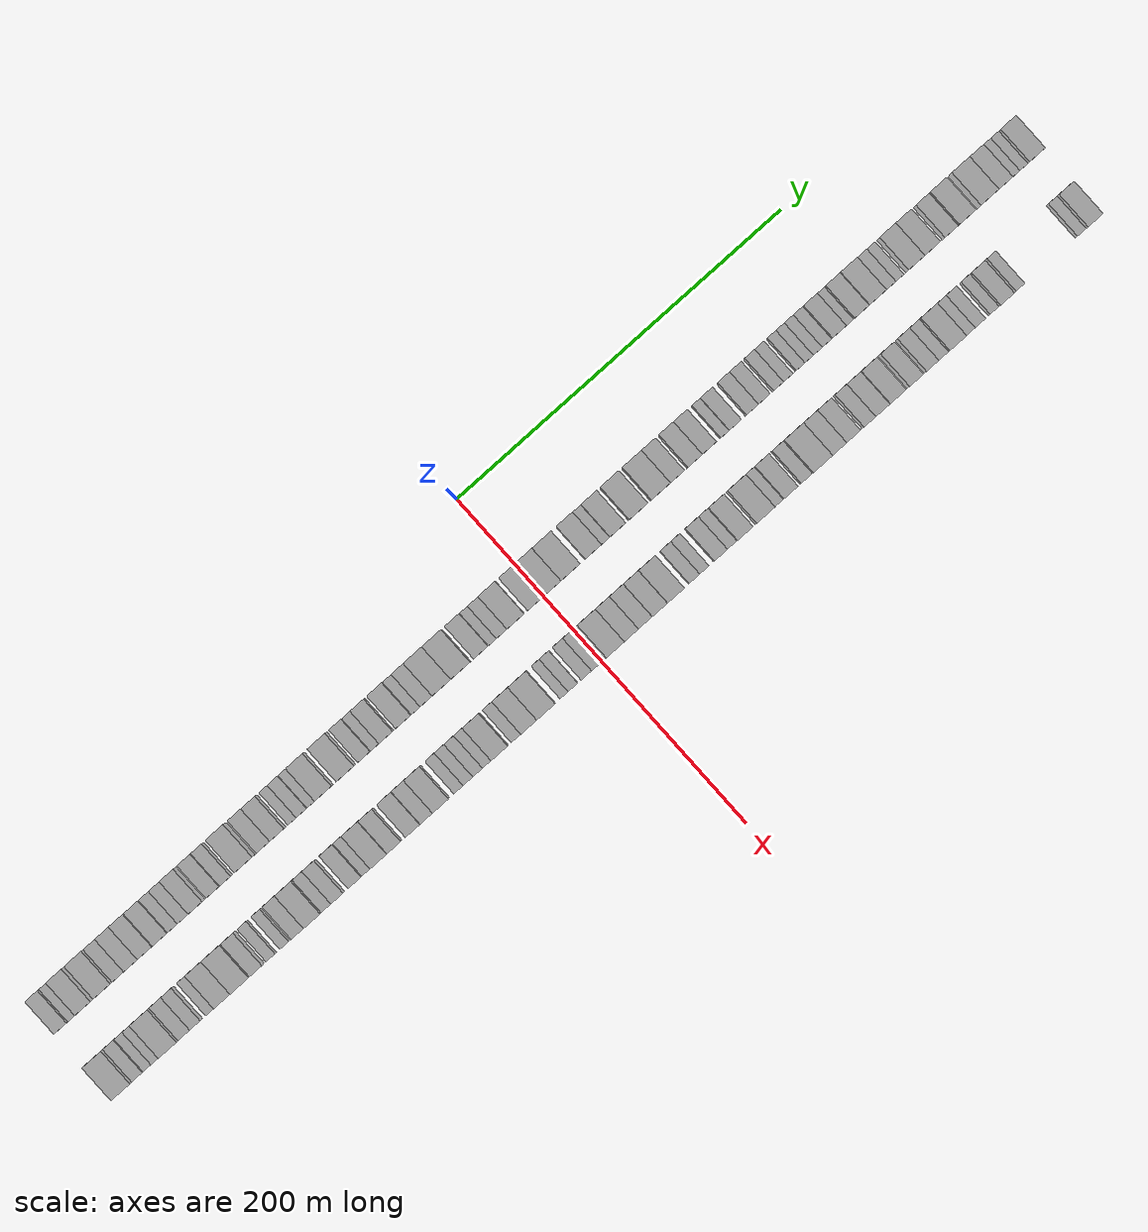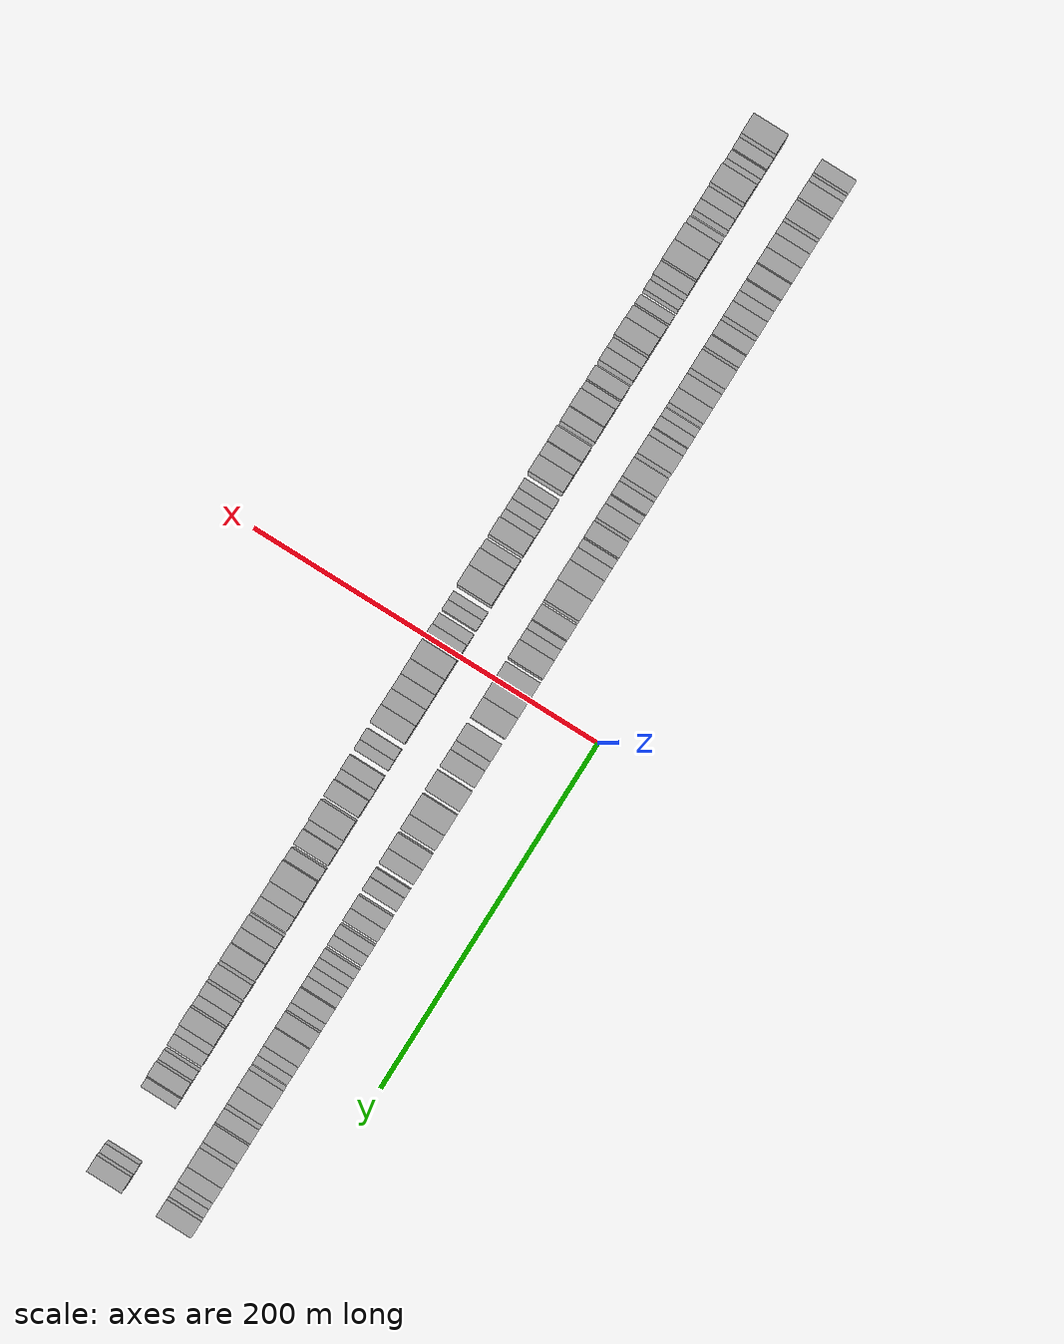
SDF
<sdf version="1.6">
 <world name="default">
  <scene>
   <sky><clouds><speed>12</speed></clouds></sky>
   <ambient>0.4 0.4 0.4 1</ambient>
   <background>0.7 0.7 0.7 1</background>
   <shadows>1</shadows>
  </scene>
  <gravity>0 0 -9.8066</gravity>
  <magnetic_field>6e-06 2.3e-05 -4.2e-05</magnetic_field>
  <physics default="0" name="default_physics" type="ode">
   <ode>
    <solver>
     <type>quick</type>
     <iters>10</iters>
     <sor>1.0</sor>
     <use_dynamic_moi_rescaling>0</use_dynamic_moi_rescaling>
    </solver>
    <constraints>
     <cfm>0</cfm>
     <erp>0.2</erp>
     <contact_max_correcting_vel>100</contact_max_correcting_vel>
     <contact_surface_layer>0.001</contact_surface_layer>
    </constraints>
   </ode>
   <max_step_size>0.004</max_step_size>
   <real_time_factor>1</real_time_factor>
   <real_time_update_rate>250</real_time_update_rate>
  </physics>
  <light name="sun" type="directional">
   <pose>0 0 10 0 0 0</pose>
   <diffuse>0.8 0.8 0.8 1</diffuse>
   <specular>0.2 0.2 0.2 1</specular>
   <attenuation>
    <range>1000</range>
    <constant>0.9</constant>
    <linear>0.01</linear>
    <quadratic>0.001</quadratic>
   </attenuation>
   <direction>-0.5 0.1 -0.9</direction>
  </light>
  <model name="building_1">
   <static>1</static>
   <pose>50.0000 -296.1191 0 0.000000 0.000000 0.000000</pose>
   <link name="link">
    <pose>0 0 9.00 0 0 0</pose>
    <collision name="collision"><geometry><box><size>20.0000 7.7617 18.0000</size></box></geometry></collision>
    <visual name="visual">
     <cast_shadows>0</cast_shadows>
     <geometry><box><size>20.0000 7.7617 18.0000</size></box></geometry>
     <material>
      <script>
       <uri>model://HANNAS_wall/materials/scripts</uri>
       <uri>model://HANNAS_wall/materials/textures</uri>
       <name>vrc/HANNAS_wall</name>
      </script>
     </material>
    </visual>
   </link>
  </model>
  <model name="building_2">
   <static>1</static>
   <pose>50.0000 -289.5064 0 0.000000 0.000000 0.000000</pose>
   <link name="link">
    <pose>0 0 6.00 0 0 0</pose>
    <collision name="collision"><geometry><box><size>20.0000 5.4638 12.0000</size></box></geometry></collision>
    <visual name="visual">
     <cast_shadows>0</cast_shadows>
     <geometry><box><size>20.0000 5.4638 12.0000</size></box></geometry>
     <material>
      <script>
       <uri>model://HANNAS_wall/materials/scripts</uri>
       <uri>model://HANNAS_wall/materials/textures</uri>
       <name>vrc/HANNAS_wall</name>
      </script>
     </material>
    </visual>
   </link>
  </model>
  <model name="building_3">
   <static>1</static>
   <pose>50.0000 -281.9822 0 0.000000 0.000000 0.000000</pose>
   <link name="link">
    <pose>0 0 10.50 0 0 0</pose>
    <collision name="collision"><geometry><box><size>20.0000 9.5846 21.0000</size></box></geometry></collision>
    <visual name="visual">
     <cast_shadows>0</cast_shadows>
     <geometry><box><size>20.0000 9.5846 21.0000</size></box></geometry>
     <material>
      <script>
       <uri>model://HANNAS_wall/materials/scripts</uri>
       <uri>model://HANNAS_wall/materials/textures</uri>
       <name>vrc/HANNAS_wall</name>
      </script>
     </material>
    </visual>
   </link>
  </model>
  <model name="building_4">
   <static>1</static>
   <pose>50.0000 -269.9203 0 0.000000 0.000000 0.000000</pose>
   <link name="link">
    <pose>0 0 12.00 0 0 0</pose>
    <collision name="collision"><geometry><box><size>20.0000 10.5393 24.0000</size></box></geometry></collision>
    <visual name="visual">
     <cast_shadows>0</cast_shadows>
     <geometry><box><size>20.0000 10.5393 24.0000</size></box></geometry>
     <material>
      <script>
       <uri>model://HANNAS_wall/materials/scripts</uri>
       <uri>model://HANNAS_wall/materials/textures</uri>
       <name>vrc/HANNAS_wall</name>
      </script>
     </material>
    </visual>
   </link>
  </model>
  <model name="building_5">
   <static>1</static>
   <pose>50.0000 -260.9323 0 0.000000 0.000000 0.000000</pose>
   <link name="link">
    <pose>0 0 7.50 0 0 0</pose>
    <collision name="collision"><geometry><box><size>20.0000 7.4368 15.0000</size></box></geometry></collision>
    <visual name="visual">
     <cast_shadows>0</cast_shadows>
     <geometry><box><size>20.0000 7.4368 15.0000</size></box></geometry>
     <material>
      <script>
       <uri>model://HANNAS_wall/materials/scripts</uri>
       <uri>model://HANNAS_wall/materials/textures</uri>
       <name>vrc/HANNAS_wall</name>
      </script>
     </material>
    </visual>
   </link>
  </model>
  <model name="building_6">
   <static>1</static>
   <pose>50.0000 -252.8447 0 0.000000 0.000000 0.000000</pose>
   <link name="link">
    <pose>0 0 9.00 0 0 0</pose>
    <collision name="collision"><geometry><box><size>20.0000 8.7385 18.0000</size></box></geometry></collision>
    <visual name="visual">
     <cast_shadows>0</cast_shadows>
     <geometry><box><size>20.0000 8.7385 18.0000</size></box></geometry>
     <material>
      <script>
       <uri>model://HANNAS_wall/materials/scripts</uri>
       <uri>model://HANNAS_wall/materials/textures</uri>
       <name>vrc/HANNAS_wall</name>
      </script>
     </material>
    </visual>
   </link>
  </model>
  <model name="building_7">
   <static>1</static>
   <pose>50.0000 -244.0707 0 0.000000 0.000000 0.000000</pose>
   <link name="link">
    <pose>0 0 10.50 0 0 0</pose>
    <collision name="collision"><geometry><box><size>20.0000 8.8095 21.0000</size></box></geometry></collision>
    <visual name="visual">
     <cast_shadows>0</cast_shadows>
     <geometry><box><size>20.0000 8.8095 21.0000</size></box></geometry>
     <material>
      <script>
       <uri>model://HANNAS_wall/materials/scripts</uri>
       <uri>model://HANNAS_wall/materials/textures</uri>
       <name>vrc/HANNAS_wall</name>
      </script>
     </material>
    </visual>
   </link>
  </model>
  <model name="building_8">
   <static>1</static>
   <pose>50.0000 -235.1789 0 0.000000 0.000000 0.000000</pose>
   <link name="link">
    <pose>0 0 9.00 0 0 0</pose>
    <collision name="collision"><geometry><box><size>20.0000 8.9741 18.0000</size></box></geometry></collision>
    <visual name="visual">
     <cast_shadows>0</cast_shadows>
     <geometry><box><size>20.0000 8.9741 18.0000</size></box></geometry>
     <material>
      <script>
       <uri>model://HANNAS_wall/materials/scripts</uri>
       <uri>model://HANNAS_wall/materials/textures</uri>
       <name>vrc/HANNAS_wall</name>
      </script>
     </material>
    </visual>
   </link>
  </model>
  <model name="building_9">
   <static>1</static>
   <pose>50.0000 -227.6335 0 0.000000 0.000000 0.000000</pose>
   <link name="link">
    <pose>0 0 7.50 0 0 0</pose>
    <collision name="collision"><geometry><box><size>20.0000 6.1166 15.0000</size></box></geometry></collision>
    <visual name="visual">
     <cast_shadows>0</cast_shadows>
     <geometry><box><size>20.0000 6.1166 15.0000</size></box></geometry>
     <material>
      <script>
       <uri>model://HANNAS_wall/materials/scripts</uri>
       <uri>model://HANNAS_wall/materials/textures</uri>
       <name>vrc/HANNAS_wall</name>
      </script>
     </material>
    </visual>
   </link>
  </model>
  <model name="building_10">
   <static>1</static>
   <pose>50.0000 -220.9918 0 0.000000 0.000000 0.000000</pose>
   <link name="link">
    <pose>0 0 7.50 0 0 0</pose>
    <collision name="collision"><geometry><box><size>20.0000 7.1667 15.0000</size></box></geometry></collision>
    <visual name="visual">
     <cast_shadows>0</cast_shadows>
     <geometry><box><size>20.0000 7.1667 15.0000</size></box></geometry>
     <material>
      <script>
       <uri>model://HANNAS_wall/materials/scripts</uri>
       <uri>model://HANNAS_wall/materials/textures</uri>
       <name>vrc/HANNAS_wall</name>
      </script>
     </material>
    </visual>
   </link>
  </model>
  <model name="building_11">
   <static>1</static>
   <pose>50.0000 -213.1312 0 0.000000 0.000000 0.000000</pose>
   <link name="link">
    <pose>0 0 10.50 0 0 0</pose>
    <collision name="collision"><geometry><box><size>20.0000 8.5546 21.0000</size></box></geometry></collision>
    <visual name="visual">
     <cast_shadows>0</cast_shadows>
     <geometry><box><size>20.0000 8.5546 21.0000</size></box></geometry>
     <material>
      <script>
       <uri>model://HANNAS_wall/materials/scripts</uri>
       <uri>model://HANNAS_wall/materials/textures</uri>
       <name>vrc/HANNAS_wall</name>
      </script>
     </material>
    </visual>
   </link>
  </model>
  <model name="building_12">
   <static>1</static>
   <pose>50.0000 -202.7954 0 0.000000 0.000000 0.000000</pose>
   <link name="link">
    <pose>0 0 9.00 0 0 0</pose>
    <collision name="collision"><geometry><box><size>20.0000 8.1169 18.0000</size></box></geometry></collision>
    <visual name="visual">
     <cast_shadows>0</cast_shadows>
     <geometry><box><size>20.0000 8.1169 18.0000</size></box></geometry>
     <material>
      <script>
       <uri>model://HANNAS_wall/materials/scripts</uri>
       <uri>model://HANNAS_wall/materials/textures</uri>
       <name>vrc/HANNAS_wall</name>
      </script>
     </material>
    </visual>
   </link>
  </model>
  <model name="building_13">
   <static>1</static>
   <pose>50.0000 -195.3282 0 0.000000 0.000000 0.000000</pose>
   <link name="link">
    <pose>0 0 7.50 0 0 0</pose>
    <collision name="collision"><geometry><box><size>20.0000 6.8176 15.0000</size></box></geometry></collision>
    <visual name="visual">
     <cast_shadows>0</cast_shadows>
     <geometry><box><size>20.0000 6.8176 15.0000</size></box></geometry>
     <material>
      <script>
       <uri>model://HANNAS_wall/materials/scripts</uri>
       <uri>model://HANNAS_wall/materials/textures</uri>
       <name>vrc/HANNAS_wall</name>
      </script>
     </material>
    </visual>
   </link>
  </model>
  <model name="building_14">
   <static>1</static>
   <pose>50.0000 -183.4700 0 0.000000 0.000000 0.000000</pose>
   <link name="link">
    <pose>0 0 12.00 0 0 0</pose>
    <collision name="collision"><geometry><box><size>20.0000 10.8988 24.0000</size></box></geometry></collision>
    <visual name="visual">
     <cast_shadows>0</cast_shadows>
     <geometry><box><size>20.0000 10.8988 24.0000</size></box></geometry>
     <material>
      <script>
       <uri>model://HANNAS_wall/materials/scripts</uri>
       <uri>model://HANNAS_wall/materials/textures</uri>
       <name>vrc/HANNAS_wall</name>
      </script>
     </material>
    </visual>
   </link>
  </model>
  <model name="building_15">
   <static>1</static>
   <pose>50.0000 -171.8970 0 0.000000 0.000000 0.000000</pose>
   <link name="link">
    <pose>0 0 9.00 0 0 0</pose>
    <collision name="collision"><geometry><box><size>20.0000 8.2473 18.0000</size></box></geometry></collision>
    <visual name="visual">
     <cast_shadows>0</cast_shadows>
     <geometry><box><size>20.0000 8.2473 18.0000</size></box></geometry>
     <material>
      <script>
       <uri>model://HANNAS_wall/materials/scripts</uri>
       <uri>model://HANNAS_wall/materials/textures</uri>
       <name>vrc/HANNAS_wall</name>
      </script>
     </material>
    </visual>
   </link>
  </model>
  <model name="building_16">
   <static>1</static>
   <pose>50.0000 -163.4078 0 0.000000 0.000000 0.000000</pose>
   <link name="link">
    <pose>0 0 9.00 0 0 0</pose>
    <collision name="collision"><geometry><box><size>20.0000 8.7312 18.0000</size></box></geometry></collision>
    <visual name="visual">
     <cast_shadows>0</cast_shadows>
     <geometry><box><size>20.0000 8.7312 18.0000</size></box></geometry>
     <material>
      <script>
       <uri>model://HANNAS_wall/materials/scripts</uri>
       <uri>model://HANNAS_wall/materials/textures</uri>
       <name>vrc/HANNAS_wall</name>
      </script>
     </material>
    </visual>
   </link>
  </model>
  <model name="building_17">
   <static>1</static>
   <pose>50.0000 -154.3923 0 0.000000 0.000000 0.000000</pose>
   <link name="link">
    <pose>0 0 6.00 0 0 0</pose>
    <collision name="collision"><geometry><box><size>20.0000 5.2997 12.0000</size></box></geometry></collision>
    <visual name="visual">
     <cast_shadows>0</cast_shadows>
     <geometry><box><size>20.0000 5.2997 12.0000</size></box></geometry>
     <material>
      <script>
       <uri>model://HANNAS_wall/materials/scripts</uri>
       <uri>model://HANNAS_wall/materials/textures</uri>
       <name>vrc/HANNAS_wall</name>
      </script>
     </material>
    </visual>
   </link>
  </model>
  <model name="building_18">
   <static>1</static>
   <pose>50.0000 -148.5322 0 0.000000 0.000000 0.000000</pose>
   <link name="link">
    <pose>0 0 7.50 0 0 0</pose>
    <collision name="collision"><geometry><box><size>20.0000 6.4204 15.0000</size></box></geometry></collision>
    <visual name="visual">
     <cast_shadows>0</cast_shadows>
     <geometry><box><size>20.0000 6.4204 15.0000</size></box></geometry>
     <material>
      <script>
       <uri>model://HANNAS_wall/materials/scripts</uri>
       <uri>model://HANNAS_wall/materials/textures</uri>
       <name>vrc/HANNAS_wall</name>
      </script>
     </material>
    </visual>
   </link>
  </model>
  <model name="building_19">
   <static>1</static>
   <pose>50.0000 -142.7000 0 0.000000 0.000000 0.000000</pose>
   <link name="link">
    <pose>0 0 6.00 0 0 0</pose>
    <collision name="collision"><geometry><box><size>20.0000 5.2441 12.0000</size></box></geometry></collision>
    <visual name="visual">
     <cast_shadows>0</cast_shadows>
     <geometry><box><size>20.0000 5.2441 12.0000</size></box></geometry>
     <material>
      <script>
       <uri>model://HANNAS_wall/materials/scripts</uri>
       <uri>model://HANNAS_wall/materials/textures</uri>
       <name>vrc/HANNAS_wall</name>
      </script>
     </material>
    </visual>
   </link>
  </model>
  <model name="building_20">
   <static>1</static>
   <pose>50.0000 -134.8904 0 0.000000 0.000000 0.000000</pose>
   <link name="link">
    <pose>0 0 10.50 0 0 0</pose>
    <collision name="collision"><geometry><box><size>20.0000 10.3751 21.0000</size></box></geometry></collision>
    <visual name="visual">
     <cast_shadows>0</cast_shadows>
     <geometry><box><size>20.0000 10.3751 21.0000</size></box></geometry>
     <material>
      <script>
       <uri>model://HANNAS_wall/materials/scripts</uri>
       <uri>model://HANNAS_wall/materials/textures</uri>
       <name>vrc/HANNAS_wall</name>
      </script>
     </material>
    </visual>
   </link>
  </model>
  <model name="building_21">
   <static>1</static>
   <pose>50.0000 -121.2510 0 0.000000 0.000000 0.000000</pose>
   <link name="link">
    <pose>0 0 12.00 0 0 0</pose>
    <collision name="collision"><geometry><box><size>20.0000 10.9037 24.0000</size></box></geometry></collision>
    <visual name="visual">
     <cast_shadows>0</cast_shadows>
     <geometry><box><size>20.0000 10.9037 24.0000</size></box></geometry>
     <material>
      <script>
       <uri>model://HANNAS_wall/materials/scripts</uri>
       <uri>model://HANNAS_wall/materials/textures</uri>
       <name>vrc/HANNAS_wall</name>
      </script>
     </material>
    </visual>
   </link>
  </model>
  <model name="building_22">
   <static>1</static>
   <pose>50.0000 -110.0232 0 0.000000 0.000000 0.000000</pose>
   <link name="link">
    <pose>0 0 9.00 0 0 0</pose>
    <collision name="collision"><geometry><box><size>20.0000 7.5519 18.0000</size></box></geometry></collision>
    <visual name="visual">
     <cast_shadows>0</cast_shadows>
     <geometry><box><size>20.0000 7.5519 18.0000</size></box></geometry>
     <material>
      <script>
       <uri>model://HANNAS_wall/materials/scripts</uri>
       <uri>model://HANNAS_wall/materials/textures</uri>
       <name>vrc/HANNAS_wall</name>
      </script>
     </material>
    </visual>
   </link>
  </model>
  <model name="building_23">
   <static>1</static>
   <pose>50.0000 -103.5406 0 0.000000 0.000000 0.000000</pose>
   <link name="link">
    <pose>0 0 6.00 0 0 0</pose>
    <collision name="collision"><geometry><box><size>20.0000 5.4134 12.0000</size></box></geometry></collision>
    <visual name="visual">
     <cast_shadows>0</cast_shadows>
     <geometry><box><size>20.0000 5.4134 12.0000</size></box></geometry>
     <material>
      <script>
       <uri>model://HANNAS_wall/materials/scripts</uri>
       <uri>model://HANNAS_wall/materials/textures</uri>
       <name>vrc/HANNAS_wall</name>
      </script>
     </material>
    </visual>
   </link>
  </model>
  <model name="building_24">
   <static>1</static>
   <pose>50.0000 -96.6438 0 0.000000 0.000000 0.000000</pose>
   <link name="link">
    <pose>0 0 9.00 0 0 0</pose>
    <collision name="collision"><geometry><box><size>20.0000 8.3801 18.0000</size></box></geometry></collision>
    <visual name="visual">
     <cast_shadows>0</cast_shadows>
     <geometry><box><size>20.0000 8.3801 18.0000</size></box></geometry>
     <material>
      <script>
       <uri>model://HANNAS_wall/materials/scripts</uri>
       <uri>model://HANNAS_wall/materials/textures</uri>
       <name>vrc/HANNAS_wall</name>
      </script>
     </material>
    </visual>
   </link>
  </model>
  <model name="building_25">
   <static>1</static>
   <pose>50.0000 -85.8106 0 0.000000 0.000000 0.000000</pose>
   <link name="link">
    <pose>0 0 10.50 0 0 0</pose>
    <collision name="collision"><geometry><box><size>20.0000 9.2864 21.0000</size></box></geometry></collision>
    <visual name="visual">
     <cast_shadows>0</cast_shadows>
     <geometry><box><size>20.0000 9.2864 21.0000</size></box></geometry>
     <material>
      <script>
       <uri>model://HANNAS_wall/materials/scripts</uri>
       <uri>model://HANNAS_wall/materials/textures</uri>
       <name>vrc/HANNAS_wall</name>
      </script>
     </material>
    </visual>
   </link>
  </model>
  <model name="building_26">
   <static>1</static>
   <pose>50.0000 -78.3732 0 0.000000 0.000000 0.000000</pose>
   <link name="link">
    <pose>0 0 6.00 0 0 0</pose>
    <collision name="collision"><geometry><box><size>20.0000 5.5884 12.0000</size></box></geometry></collision>
    <visual name="visual">
     <cast_shadows>0</cast_shadows>
     <geometry><box><size>20.0000 5.5884 12.0000</size></box></geometry>
     <material>
      <script>
       <uri>model://HANNAS_wall/materials/scripts</uri>
       <uri>model://HANNAS_wall/materials/textures</uri>
       <name>vrc/HANNAS_wall</name>
      </script>
     </material>
    </visual>
   </link>
  </model>
  <model name="building_27">
   <static>1</static>
   <pose>50.0000 -71.7725 0 0.000000 0.000000 0.000000</pose>
   <link name="link">
    <pose>0 0 9.00 0 0 0</pose>
    <collision name="collision"><geometry><box><size>20.0000 7.6129 18.0000</size></box></geometry></collision>
    <visual name="visual">
     <cast_shadows>0</cast_shadows>
     <geometry><box><size>20.0000 7.6129 18.0000</size></box></geometry>
     <material>
      <script>
       <uri>model://HANNAS_wall/materials/scripts</uri>
       <uri>model://HANNAS_wall/materials/textures</uri>
       <name>vrc/HANNAS_wall</name>
      </script>
     </material>
    </visual>
   </link>
  </model>
  <model name="building_28">
   <static>1</static>
   <pose>50.0000 -62.2975 0 0.000000 0.000000 0.000000</pose>
   <link name="link">
    <pose>0 0 12.00 0 0 0</pose>
    <collision name="collision"><geometry><box><size>20.0000 11.3370 24.0000</size></box></geometry></collision>
    <visual name="visual">
     <cast_shadows>0</cast_shadows>
     <geometry><box><size>20.0000 11.3370 24.0000</size></box></geometry>
     <material>
      <script>
       <uri>model://HANNAS_wall/materials/scripts</uri>
       <uri>model://HANNAS_wall/materials/textures</uri>
       <name>vrc/HANNAS_wall</name>
      </script>
     </material>
    </visual>
   </link>
  </model>
  <model name="building_29">
   <static>1</static>
   <pose>50.0000 -50.7047 0 0.000000 0.000000 0.000000</pose>
   <link name="link">
    <pose>0 0 12.00 0 0 0</pose>
    <collision name="collision"><geometry><box><size>20.0000 11.8486 24.0000</size></box></geometry></collision>
    <visual name="visual">
     <cast_shadows>0</cast_shadows>
     <geometry><box><size>20.0000 11.8486 24.0000</size></box></geometry>
     <material>
      <script>
       <uri>model://HANNAS_wall/materials/scripts</uri>
       <uri>model://HANNAS_wall/materials/textures</uri>
       <name>vrc/HANNAS_wall</name>
      </script>
     </material>
    </visual>
   </link>
  </model>
  <model name="building_30">
   <static>1</static>
   <pose>50.0000 -38.3129 0 0.000000 0.000000 0.000000</pose>
   <link name="link">
    <pose>0 0 10.50 0 0 0</pose>
    <collision name="collision"><geometry><box><size>20.0000 8.9351 21.0000</size></box></geometry></collision>
    <visual name="visual">
     <cast_shadows>0</cast_shadows>
     <geometry><box><size>20.0000 8.9351 21.0000</size></box></geometry>
     <material>
      <script>
       <uri>model://HANNAS_wall/materials/scripts</uri>
       <uri>model://HANNAS_wall/materials/textures</uri>
       <name>vrc/HANNAS_wall</name>
      </script>
     </material>
    </visual>
   </link>
  </model>
  <model name="building_31">
   <static>1</static>
   <pose>50.0000 -31.3603 0 0.000000 0.000000 0.000000</pose>
   <link name="link">
    <pose>0 0 6.00 0 0 0</pose>
    <collision name="collision"><geometry><box><size>20.0000 4.9701 12.0000</size></box></geometry></collision>
    <visual name="visual">
     <cast_shadows>0</cast_shadows>
     <geometry><box><size>20.0000 4.9701 12.0000</size></box></geometry>
     <material>
      <script>
       <uri>model://HANNAS_wall/materials/scripts</uri>
       <uri>model://HANNAS_wall/materials/textures</uri>
       <name>vrc/HANNAS_wall</name>
      </script>
     </material>
    </visual>
   </link>
  </model>
  <model name="building_32">
   <static>1</static>
   <pose>50.0000 -25.5734 0 0.000000 0.000000 0.000000</pose>
   <link name="link">
    <pose>0 0 7.50 0 0 0</pose>
    <collision name="collision"><geometry><box><size>20.0000 6.6037 15.0000</size></box></geometry></collision>
    <visual name="visual">
     <cast_shadows>0</cast_shadows>
     <geometry><box><size>20.0000 6.6037 15.0000</size></box></geometry>
     <material>
      <script>
       <uri>model://HANNAS_wall/materials/scripts</uri>
       <uri>model://HANNAS_wall/materials/textures</uri>
       <name>vrc/HANNAS_wall</name>
      </script>
     </material>
    </visual>
   </link>
  </model>
  <model name="building_33">
   <static>1</static>
   <pose>50.0000 -17.0000 0 0.000000 0.000000 0.000000</pose>
   <link name="link">
    <pose>0 0 12.00 0 0 0</pose>
    <collision name="collision"><geometry><box><size>20.0000 10.5430 24.0000</size></box></geometry></collision>
    <visual name="visual">
     <cast_shadows>0</cast_shadows>
     <geometry><box><size>20.0000 10.5430 24.0000</size></box></geometry>
     <material>
      <script>
       <uri>model://HANNAS_wall/materials/scripts</uri>
       <uri>model://HANNAS_wall/materials/textures</uri>
       <name>vrc/HANNAS_wall</name>
      </script>
     </material>
    </visual>
   </link>
  </model>
  <model name="building_34">
   <static>1</static>
   <pose>50.0000 -5.1855 0 0.000000 0.000000 0.000000</pose>
   <link name="link">
    <pose>0 0 10.50 0 0 0</pose>
    <collision name="collision"><geometry><box><size>20.0000 9.0860 21.0000</size></box></geometry></collision>
    <visual name="visual">
     <cast_shadows>0</cast_shadows>
     <geometry><box><size>20.0000 9.0860 21.0000</size></box></geometry>
     <material>
      <script>
       <uri>model://HANNAS_wall/materials/scripts</uri>
       <uri>model://HANNAS_wall/materials/textures</uri>
       <name>vrc/HANNAS_wall</name>
      </script>
     </material>
    </visual>
   </link>
  </model>
  <model name="building_35">
   <static>1</static>
   <pose>50.0000 6.0593 0 0.000000 0.000000 0.000000</pose>
   <link name="link">
    <pose>0 0 10.50 0 0 0</pose>
    <collision name="collision"><geometry><box><size>20.0000 9.4036 21.0000</size></box></geometry></collision>
    <visual name="visual">
     <cast_shadows>0</cast_shadows>
     <geometry><box><size>20.0000 9.4036 21.0000</size></box></geometry>
     <material>
      <script>
       <uri>model://HANNAS_wall/materials/scripts</uri>
       <uri>model://HANNAS_wall/materials/textures</uri>
       <name>vrc/HANNAS_wall</name>
      </script>
     </material>
    </visual>
   </link>
  </model>
  <model name="building_36">
   <static>1</static>
   <pose>50.0000 16.6558 0 0.000000 0.000000 0.000000</pose>
   <link name="link">
    <pose>0 0 12.00 0 0 0</pose>
    <collision name="collision"><geometry><box><size>20.0000 11.7895 24.0000</size></box></geometry></collision>
    <visual name="visual">
     <cast_shadows>0</cast_shadows>
     <geometry><box><size>20.0000 11.7895 24.0000</size></box></geometry>
     <material>
      <script>
       <uri>model://HANNAS_wall/materials/scripts</uri>
       <uri>model://HANNAS_wall/materials/textures</uri>
       <name>vrc/HANNAS_wall</name>
      </script>
     </material>
    </visual>
   </link>
  </model>
  <model name="building_37">
   <static>1</static>
   <pose>50.0000 30.5757 0 0.000000 0.000000 0.000000</pose>
   <link name="link">
    <pose>0 0 12.00 0 0 0</pose>
    <collision name="collision"><geometry><box><size>20.0000 10.0503 24.0000</size></box></geometry></collision>
    <visual name="visual">
     <cast_shadows>0</cast_shadows>
     <geometry><box><size>20.0000 10.0503 24.0000</size></box></geometry>
     <material>
      <script>
       <uri>model://HANNAS_wall/materials/scripts</uri>
       <uri>model://HANNAS_wall/materials/textures</uri>
       <name>vrc/HANNAS_wall</name>
      </script>
     </material>
    </visual>
   </link>
  </model>
  <model name="building_38">
   <static>1</static>
   <pose>50.0000 38.1745 0 0.000000 0.000000 0.000000</pose>
   <link name="link">
    <pose>0 0 6.00 0 0 0</pose>
    <collision name="collision"><geometry><box><size>20.0000 5.1472 12.0000</size></box></geometry></collision>
    <visual name="visual">
     <cast_shadows>0</cast_shadows>
     <geometry><box><size>20.0000 5.1472 12.0000</size></box></geometry>
     <material>
      <script>
       <uri>model://HANNAS_wall/materials/scripts</uri>
       <uri>model://HANNAS_wall/materials/textures</uri>
       <name>vrc/HANNAS_wall</name>
      </script>
     </material>
    </visual>
   </link>
  </model>
  <model name="building_39">
   <static>1</static>
   <pose>50.0000 45.6033 0 0.000000 0.000000 0.000000</pose>
   <link name="link">
    <pose>0 0 10.50 0 0 0</pose>
    <collision name="collision"><geometry><box><size>20.0000 9.7105 21.0000</size></box></geometry></collision>
    <visual name="visual">
     <cast_shadows>0</cast_shadows>
     <geometry><box><size>20.0000 9.7105 21.0000</size></box></geometry>
     <material>
      <script>
       <uri>model://HANNAS_wall/materials/scripts</uri>
       <uri>model://HANNAS_wall/materials/textures</uri>
       <name>vrc/HANNAS_wall</name>
      </script>
     </material>
    </visual>
   </link>
  </model>
  <model name="building_40">
   <static>1</static>
   <pose>50.0000 58.2262 0 0.000000 0.000000 0.000000</pose>
   <link name="link">
    <pose>0 0 12.00 0 0 0</pose>
    <collision name="collision"><geometry><box><size>20.0000 11.5352 24.0000</size></box></geometry></collision>
    <visual name="visual">
     <cast_shadows>0</cast_shadows>
     <geometry><box><size>20.0000 11.5352 24.0000</size></box></geometry>
     <material>
      <script>
       <uri>model://HANNAS_wall/materials/scripts</uri>
       <uri>model://HANNAS_wall/materials/textures</uri>
       <name>vrc/HANNAS_wall</name>
      </script>
     </material>
    </visual>
   </link>
  </model>
  <model name="building_41">
   <static>1</static>
   <pose>50.0000 71.8570 0 0.000000 0.000000 0.000000</pose>
   <link name="link">
    <pose>0 0 12.00 0 0 0</pose>
    <collision name="collision"><geometry><box><size>20.0000 11.7263 24.0000</size></box></geometry></collision>
    <visual name="visual">
     <cast_shadows>0</cast_shadows>
     <geometry><box><size>20.0000 11.7263 24.0000</size></box></geometry>
     <material>
      <script>
       <uri>model://HANNAS_wall/materials/scripts</uri>
       <uri>model://HANNAS_wall/materials/textures</uri>
       <name>vrc/HANNAS_wall</name>
      </script>
     </material>
    </visual>
   </link>
  </model>
  <model name="building_42">
   <static>1</static>
   <pose>50.0000 82.0700 0 0.000000 0.000000 0.000000</pose>
   <link name="link">
    <pose>0 0 10.50 0 0 0</pose>
    <collision name="collision"><geometry><box><size>20.0000 8.6996 21.0000</size></box></geometry></collision>
    <visual name="visual">
     <cast_shadows>0</cast_shadows>
     <geometry><box><size>20.0000 8.6996 21.0000</size></box></geometry>
     <material>
      <script>
       <uri>model://HANNAS_wall/materials/scripts</uri>
       <uri>model://HANNAS_wall/materials/textures</uri>
       <name>vrc/HANNAS_wall</name>
      </script>
     </material>
    </visual>
   </link>
  </model>
  <model name="building_43">
   <static>1</static>
   <pose>50.0000 92.8942 0 0.000000 0.000000 0.000000</pose>
   <link name="link">
    <pose>0 0 10.50 0 0 0</pose>
    <collision name="collision"><geometry><box><size>20.0000 8.9489 21.0000</size></box></geometry></collision>
    <visual name="visual">
     <cast_shadows>0</cast_shadows>
     <geometry><box><size>20.0000 8.9489 21.0000</size></box></geometry>
     <material>
      <script>
       <uri>model://HANNAS_wall/materials/scripts</uri>
       <uri>model://HANNAS_wall/materials/textures</uri>
       <name>vrc/HANNAS_wall</name>
      </script>
     </material>
    </visual>
   </link>
  </model>
  <model name="building_44">
   <static>1</static>
   <pose>50.0000 101.6525 0 0.000000 0.000000 0.000000</pose>
   <link name="link">
    <pose>0 0 10.50 0 0 0</pose>
    <collision name="collision"><geometry><box><size>20.0000 8.5676 21.0000</size></box></geometry></collision>
    <visual name="visual">
     <cast_shadows>0</cast_shadows>
     <geometry><box><size>20.0000 8.5676 21.0000</size></box></geometry>
     <material>
      <script>
       <uri>model://HANNAS_wall/materials/scripts</uri>
       <uri>model://HANNAS_wall/materials/textures</uri>
       <name>vrc/HANNAS_wall</name>
      </script>
     </material>
    </visual>
   </link>
  </model>
  <model name="building_45">
   <static>1</static>
   <pose>50.0000 111.4950 0 0.000000 0.000000 0.000000</pose>
   <link name="link">
    <pose>0 0 6.00 0 0 0</pose>
    <collision name="collision"><geometry><box><size>20.0000 5.1174 12.0000</size></box></geometry></collision>
    <visual name="visual">
     <cast_shadows>0</cast_shadows>
     <geometry><box><size>20.0000 5.1174 12.0000</size></box></geometry>
     <material>
      <script>
       <uri>model://HANNAS_wall/materials/scripts</uri>
       <uri>model://HANNAS_wall/materials/textures</uri>
       <name>vrc/HANNAS_wall</name>
      </script>
     </material>
    </visual>
   </link>
  </model>
  <model name="building_46">
   <static>1</static>
   <pose>50.0000 117.8021 0 0.000000 0.000000 0.000000</pose>
   <link name="link">
    <pose>0 0 7.50 0 0 0</pose>
    <collision name="collision"><geometry><box><size>20.0000 7.4967 15.0000</size></box></geometry></collision>
    <visual name="visual">
     <cast_shadows>0</cast_shadows>
     <geometry><box><size>20.0000 7.4967 15.0000</size></box></geometry>
     <material>
      <script>
       <uri>model://HANNAS_wall/materials/scripts</uri>
       <uri>model://HANNAS_wall/materials/textures</uri>
       <name>vrc/HANNAS_wall</name>
      </script>
     </material>
    </visual>
   </link>
  </model>
  <model name="building_47">
   <static>1</static>
   <pose>50.0000 128.2664 0 0.000000 0.000000 0.000000</pose>
   <link name="link">
    <pose>0 0 7.50 0 0 0</pose>
    <collision name="collision"><geometry><box><size>20.0000 7.4319 15.0000</size></box></geometry></collision>
    <visual name="visual">
     <cast_shadows>0</cast_shadows>
     <geometry><box><size>20.0000 7.4319 15.0000</size></box></geometry>
     <material>
      <script>
       <uri>model://HANNAS_wall/materials/scripts</uri>
       <uri>model://HANNAS_wall/materials/textures</uri>
       <name>vrc/HANNAS_wall</name>
      </script>
     </material>
    </visual>
   </link>
  </model>
  <model name="building_48">
   <static>1</static>
   <pose>50.0000 135.5950 0 0.000000 0.000000 0.000000</pose>
   <link name="link">
    <pose>0 0 7.50 0 0 0</pose>
    <collision name="collision"><geometry><box><size>20.0000 7.2254 15.0000</size></box></geometry></collision>
    <visual name="visual">
     <cast_shadows>0</cast_shadows>
     <geometry><box><size>20.0000 7.2254 15.0000</size></box></geometry>
     <material>
      <script>
       <uri>model://HANNAS_wall/materials/scripts</uri>
       <uri>model://HANNAS_wall/materials/textures</uri>
       <name>vrc/HANNAS_wall</name>
      </script>
     </material>
    </visual>
   </link>
  </model>
  <model name="building_49">
   <static>1</static>
   <pose>50.0000 144.2741 0 0.000000 0.000000 0.000000</pose>
   <link name="link">
    <pose>0 0 7.50 0 0 0</pose>
    <collision name="collision"><geometry><box><size>20.0000 6.1329 15.0000</size></box></geometry></collision>
    <visual name="visual">
     <cast_shadows>0</cast_shadows>
     <geometry><box><size>20.0000 6.1329 15.0000</size></box></geometry>
     <material>
      <script>
       <uri>model://HANNAS_wall/materials/scripts</uri>
       <uri>model://HANNAS_wall/materials/textures</uri>
       <name>vrc/HANNAS_wall</name>
      </script>
     </material>
    </visual>
   </link>
  </model>
  <model name="building_50">
   <static>1</static>
   <pose>50.0000 150.3079 0 0.000000 0.000000 0.000000</pose>
   <link name="link">
    <pose>0 0 6.00 0 0 0</pose>
    <collision name="collision"><geometry><box><size>20.0000 5.9346 12.0000</size></box></geometry></collision>
    <visual name="visual">
     <cast_shadows>0</cast_shadows>
     <geometry><box><size>20.0000 5.9346 12.0000</size></box></geometry>
     <material>
      <script>
       <uri>model://HANNAS_wall/materials/scripts</uri>
       <uri>model://HANNAS_wall/materials/textures</uri>
       <name>vrc/HANNAS_wall</name>
      </script>
     </material>
    </visual>
   </link>
  </model>
  <model name="building_51">
   <static>1</static>
   <pose>50.0000 157.9339 0 0.000000 0.000000 0.000000</pose>
   <link name="link">
    <pose>0 0 6.00 0 0 0</pose>
    <collision name="collision"><geometry><box><size>20.0000 5.3174 12.0000</size></box></geometry></collision>
    <visual name="visual">
     <cast_shadows>0</cast_shadows>
     <geometry><box><size>20.0000 5.3174 12.0000</size></box></geometry>
     <material>
      <script>
       <uri>model://HANNAS_wall/materials/scripts</uri>
       <uri>model://HANNAS_wall/materials/textures</uri>
       <name>vrc/HANNAS_wall</name>
      </script>
     </material>
    </visual>
   </link>
  </model>
  <model name="building_52">
   <static>1</static>
   <pose>50.0000 163.1805 0 0.000000 0.000000 0.000000</pose>
   <link name="link">
    <pose>0 0 6.00 0 0 0</pose>
    <collision name="collision"><geometry><box><size>20.0000 5.1758 12.0000</size></box></geometry></collision>
    <visual name="visual">
     <cast_shadows>0</cast_shadows>
     <geometry><box><size>20.0000 5.1758 12.0000</size></box></geometry>
     <material>
      <script>
       <uri>model://HANNAS_wall/materials/scripts</uri>
       <uri>model://HANNAS_wall/materials/textures</uri>
       <name>vrc/HANNAS_wall</name>
      </script>
     </material>
    </visual>
   </link>
  </model>
  <model name="building_53">
   <static>1</static>
   <pose>50.0000 168.5119 0 0.000000 0.000000 0.000000</pose>
   <link name="link">
    <pose>0 0 6.00 0 0 0</pose>
    <collision name="collision"><geometry><box><size>20.0000 5.4871 12.0000</size></box></geometry></collision>
    <visual name="visual">
     <cast_shadows>0</cast_shadows>
     <geometry><box><size>20.0000 5.4871 12.0000</size></box></geometry>
     <material>
      <script>
       <uri>model://HANNAS_wall/materials/scripts</uri>
       <uri>model://HANNAS_wall/materials/textures</uri>
       <name>vrc/HANNAS_wall</name>
      </script>
     </material>
    </visual>
   </link>
  </model>
  <model name="building_54">
   <static>1</static>
   <pose>50.0000 174.1888 0 0.000000 0.000000 0.000000</pose>
   <link name="link">
    <pose>0 0 6.00 0 0 0</pose>
    <collision name="collision"><geometry><box><size>20.0000 5.8667 12.0000</size></box></geometry></collision>
    <visual name="visual">
     <cast_shadows>0</cast_shadows>
     <geometry><box><size>20.0000 5.8667 12.0000</size></box></geometry>
     <material>
      <script>
       <uri>model://HANNAS_wall/materials/scripts</uri>
       <uri>model://HANNAS_wall/materials/textures</uri>
       <name>vrc/HANNAS_wall</name>
      </script>
     </material>
    </visual>
   </link>
  </model>
  <model name="building_55">
   <static>1</static>
   <pose>50.0000 181.3988 0 0.000000 0.000000 0.000000</pose>
   <link name="link">
    <pose>0 0 9.00 0 0 0</pose>
    <collision name="collision"><geometry><box><size>20.0000 8.5532 18.0000</size></box></geometry></collision>
    <visual name="visual">
     <cast_shadows>0</cast_shadows>
     <geometry><box><size>20.0000 8.5532 18.0000</size></box></geometry>
     <material>
      <script>
       <uri>model://HANNAS_wall/materials/scripts</uri>
       <uri>model://HANNAS_wall/materials/textures</uri>
       <name>vrc/HANNAS_wall</name>
      </script>
     </material>
    </visual>
   </link>
  </model>
  <model name="building_56">
   <static>1</static>
   <pose>50.0000 188.0860 0 0.000000 0.000000 0.000000</pose>
   <link name="link">
    <pose>0 0 6.00 0 0 0</pose>
    <collision name="collision"><geometry><box><size>20.0000 4.8214 12.0000</size></box></geometry></collision>
    <visual name="visual">
     <cast_shadows>0</cast_shadows>
     <geometry><box><size>20.0000 4.8214 12.0000</size></box></geometry>
     <material>
      <script>
       <uri>model://HANNAS_wall/materials/scripts</uri>
       <uri>model://HANNAS_wall/materials/textures</uri>
       <name>vrc/HANNAS_wall</name>
      </script>
     </material>
    </visual>
   </link>
  </model>
  <model name="building_57">
   <static>1</static>
   <pose>50.0000 194.9580 0 0.000000 0.000000 0.000000</pose>
   <link name="link">
    <pose>0 0 10.50 0 0 0</pose>
    <collision name="collision"><geometry><box><size>20.0000 8.9225 21.0000</size></box></geometry></collision>
    <visual name="visual">
     <cast_shadows>0</cast_shadows>
     <geometry><box><size>20.0000 8.9225 21.0000</size></box></geometry>
     <material>
      <script>
       <uri>model://HANNAS_wall/materials/scripts</uri>
       <uri>model://HANNAS_wall/materials/textures</uri>
       <name>vrc/HANNAS_wall</name>
      </script>
     </material>
    </visual>
   </link>
  </model>
  <model name="building_58">
   <static>1</static>
   <pose>50.0000 204.5758 0 0.000000 0.000000 0.000000</pose>
   <link name="link">
    <pose>0 0 12.00 0 0 0</pose>
    <collision name="collision"><geometry><box><size>20.0000 10.3131 24.0000</size></box></geometry></collision>
    <visual name="visual">
     <cast_shadows>0</cast_shadows>
     <geometry><box><size>20.0000 10.3131 24.0000</size></box></geometry>
     <material>
      <script>
       <uri>model://HANNAS_wall/materials/scripts</uri>
       <uri>model://HANNAS_wall/materials/textures</uri>
       <name>vrc/HANNAS_wall</name>
      </script>
     </material>
    </visual>
   </link>
  </model>
  <model name="building_59">
   <static>1</static>
   <pose>50.0000 212.9830 0 0.000000 0.000000 0.000000</pose>
   <link name="link">
    <pose>0 0 7.50 0 0 0</pose>
    <collision name="collision"><geometry><box><size>20.0000 6.5013 15.0000</size></box></geometry></collision>
    <visual name="visual">
     <cast_shadows>0</cast_shadows>
     <geometry><box><size>20.0000 6.5013 15.0000</size></box></geometry>
     <material>
      <script>
       <uri>model://HANNAS_wall/materials/scripts</uri>
       <uri>model://HANNAS_wall/materials/textures</uri>
       <name>vrc/HANNAS_wall</name>
      </script>
     </material>
    </visual>
   </link>
  </model>
  <model name="building_60">
   <static>1</static>
   <pose>50.0000 218.8792 0 0.000000 0.000000 0.000000</pose>
   <link name="link">
    <pose>0 0 6.00 0 0 0</pose>
    <collision name="collision"><geometry><box><size>20.0000 5.2910 12.0000</size></box></geometry></collision>
    <visual name="visual">
     <cast_shadows>0</cast_shadows>
     <geometry><box><size>20.0000 5.2910 12.0000</size></box></geometry>
     <material>
      <script>
       <uri>model://HANNAS_wall/materials/scripts</uri>
       <uri>model://HANNAS_wall/materials/textures</uri>
       <name>vrc/HANNAS_wall</name>
      </script>
     </material>
    </visual>
   </link>
  </model>
  <model name="building_61">
   <static>1</static>
   <pose>50.0000 228.4953 0 0.000000 0.000000 0.000000</pose>
   <link name="link">
    <pose>0 0 10.50 0 0 0</pose>
    <collision name="collision"><geometry><box><size>20.0000 9.9412 21.0000</size></box></geometry></collision>
    <visual name="visual">
     <cast_shadows>0</cast_shadows>
     <geometry><box><size>20.0000 9.9412 21.0000</size></box></geometry>
     <material>
      <script>
       <uri>model://HANNAS_wall/materials/scripts</uri>
       <uri>model://HANNAS_wall/materials/textures</uri>
       <name>vrc/HANNAS_wall</name>
      </script>
     </material>
    </visual>
   </link>
  </model>
  <model name="building_62">
   <static>1</static>
   <pose>50.0000 238.2640 0 0.000000 0.000000 0.000000</pose>
   <link name="link">
    <pose>0 0 10.50 0 0 0</pose>
    <collision name="collision"><geometry><box><size>20.0000 9.5962 21.0000</size></box></geometry></collision>
    <visual name="visual">
     <cast_shadows>0</cast_shadows>
     <geometry><box><size>20.0000 9.5962 21.0000</size></box></geometry>
     <material>
      <script>
       <uri>model://HANNAS_wall/materials/scripts</uri>
       <uri>model://HANNAS_wall/materials/textures</uri>
       <name>vrc/HANNAS_wall</name>
      </script>
     </material>
    </visual>
   </link>
  </model>
  <model name="building_63">
   <static>1</static>
   <pose>50.0000 250.1538 0 0.000000 0.000000 0.000000</pose>
   <link name="link">
    <pose>0 0 9.00 0 0 0</pose>
    <collision name="collision"><geometry><box><size>20.0000 8.1834 18.0000</size></box></geometry></collision>
    <visual name="visual">
     <cast_shadows>0</cast_shadows>
     <geometry><box><size>20.0000 8.1834 18.0000</size></box></geometry>
     <material>
      <script>
       <uri>model://HANNAS_wall/materials/scripts</uri>
       <uri>model://HANNAS_wall/materials/textures</uri>
       <name>vrc/HANNAS_wall</name>
      </script>
     </material>
    </visual>
   </link>
  </model>
  <model name="building_64">
   <static>1</static>
   <pose>50.0000 259.3626 0 0.000000 0.000000 0.000000</pose>
   <link name="link">
    <pose>0 0 12.00 0 0 0</pose>
    <collision name="collision"><geometry><box><size>20.0000 10.2342 24.0000</size></box></geometry></collision>
    <visual name="visual">
     <cast_shadows>0</cast_shadows>
     <geometry><box><size>20.0000 10.2342 24.0000</size></box></geometry>
     <material>
      <script>
       <uri>model://HANNAS_wall/materials/scripts</uri>
       <uri>model://HANNAS_wall/materials/textures</uri>
       <name>vrc/HANNAS_wall</name>
      </script>
     </material>
    </visual>
   </link>
  </model>
  <model name="building_65">
   <static>1</static>
   <pose>50.0000 272.9652 0 0.000000 0.000000 0.000000</pose>
   <link name="link">
    <pose>0 0 12.00 0 0 0</pose>
    <collision name="collision"><geometry><box><size>20.0000 10.9709 24.0000</size></box></geometry></collision>
    <visual name="visual">
     <cast_shadows>0</cast_shadows>
     <geometry><box><size>20.0000 10.9709 24.0000</size></box></geometry>
     <material>
      <script>
       <uri>model://HANNAS_wall/materials/scripts</uri>
       <uri>model://HANNAS_wall/materials/textures</uri>
       <name>vrc/HANNAS_wall</name>
      </script>
     </material>
    </visual>
   </link>
  </model>
  <model name="building_66">
   <static>1</static>
   <pose>50.0000 282.8895 0 0.000000 0.000000 0.000000</pose>
   <link name="link">
    <pose>0 0 10.50 0 0 0</pose>
    <collision name="collision"><geometry><box><size>20.0000 8.8778 21.0000</size></box></geometry></collision>
    <visual name="visual">
     <cast_shadows>0</cast_shadows>
     <geometry><box><size>20.0000 8.8778 21.0000</size></box></geometry>
     <material>
      <script>
       <uri>model://HANNAS_wall/materials/scripts</uri>
       <uri>model://HANNAS_wall/materials/textures</uri>
       <name>vrc/HANNAS_wall</name>
      </script>
     </material>
    </visual>
   </link>
  </model>
  <model name="building_67">
   <static>1</static>
   <pose>50.0000 289.9870 0 0.000000 0.000000 0.000000</pose>
   <link name="link">
    <pose>0 0 6.00 0 0 0</pose>
    <collision name="collision"><geometry><box><size>20.0000 5.3170 12.0000</size></box></geometry></collision>
    <visual name="visual">
     <cast_shadows>0</cast_shadows>
     <geometry><box><size>20.0000 5.3170 12.0000</size></box></geometry>
     <material>
      <script>
       <uri>model://HANNAS_wall/materials/scripts</uri>
       <uri>model://HANNAS_wall/materials/textures</uri>
       <name>vrc/HANNAS_wall</name>
      </script>
     </material>
    </visual>
   </link>
  </model>
  <model name="building_68">
   <static>1</static>
   <pose>50.0000 295.0909 0 0.000000 0.000000 0.000000</pose>
   <link name="link">
    <pose>0 0 6.00 0 0 0</pose>
    <collision name="collision"><geometry><box><size>20.0000 4.8909 12.0000</size></box></geometry></collision>
    <visual name="visual">
     <cast_shadows>0</cast_shadows>
     <geometry><box><size>20.0000 4.8909 12.0000</size></box></geometry>
     <material>
      <script>
       <uri>model://HANNAS_wall/materials/scripts</uri>
       <uri>model://HANNAS_wall/materials/textures</uri>
       <name>vrc/HANNAS_wall</name>
      </script>
     </material>
    </visual>
   </link>
  </model>
  <model name="building_69">
   <static>1</static>
   <pose>50.0000 302.3529 0 0.000000 0.000000 0.000000</pose>
   <link name="link">
    <pose>0 0 10.50 0 0 0</pose>
    <collision name="collision"><geometry><box><size>20.0000 9.6330 21.0000</size></box></geometry></collision>
    <visual name="visual">
     <cast_shadows>0</cast_shadows>
     <geometry><box><size>20.0000 9.6330 21.0000</size></box></geometry>
     <material>
      <script>
       <uri>model://HANNAS_wall/materials/scripts</uri>
       <uri>model://HANNAS_wall/materials/textures</uri>
       <name>vrc/HANNAS_wall</name>
      </script>
     </material>
    </visual>
   </link>
  </model>
  <model name="building_70">
   <static>1</static>
   <pose>90.0000 -294.2037 0 0.000000 0.000000 0.000000</pose>
   <link name="link">
    <pose>0 0 12.00 0 0 0</pose>
    <collision name="collision"><geometry><box><size>20.0000 11.5926 24.0000</size></box></geometry></collision>
    <visual name="visual">
     <cast_shadows>0</cast_shadows>
     <geometry><box><size>20.0000 11.5926 24.0000</size></box></geometry>
     <material>
      <script>
       <uri>model://HANNAS_wall/materials/scripts</uri>
       <uri>model://HANNAS_wall/materials/textures</uri>
       <name>vrc/HANNAS_wall</name>
      </script>
     </material>
    </visual>
   </link>
  </model>
  <model name="building_71">
   <static>1</static>
   <pose>90.0000 -285.1056 0 0.000000 0.000000 0.000000</pose>
   <link name="link">
    <pose>0 0 7.50 0 0 0</pose>
    <collision name="collision"><geometry><box><size>20.0000 6.6035 15.0000</size></box></geometry></collision>
    <visual name="visual">
     <cast_shadows>0</cast_shadows>
     <geometry><box><size>20.0000 6.6035 15.0000</size></box></geometry>
     <material>
      <script>
       <uri>model://HANNAS_wall/materials/scripts</uri>
       <uri>model://HANNAS_wall/materials/textures</uri>
       <name>vrc/HANNAS_wall</name>
      </script>
     </material>
    </visual>
   </link>
  </model>
  <model name="building_72">
   <static>1</static>
   <pose>90.0000 -279.3590 0 0.000000 0.000000 0.000000</pose>
   <link name="link">
    <pose>0 0 6.00 0 0 0</pose>
    <collision name="collision"><geometry><box><size>20.0000 4.8897 12.0000</size></box></geometry></collision>
    <visual name="visual">
     <cast_shadows>0</cast_shadows>
     <geometry><box><size>20.0000 4.8897 12.0000</size></box></geometry>
     <material>
      <script>
       <uri>model://HANNAS_wall/materials/scripts</uri>
       <uri>model://HANNAS_wall/materials/textures</uri>
       <name>vrc/HANNAS_wall</name>
      </script>
     </material>
    </visual>
   </link>
  </model>
  <model name="building_73">
   <static>1</static>
   <pose>90.0000 -273.9968 0 0.000000 0.000000 0.000000</pose>
   <link name="link">
    <pose>0 0 6.00 0 0 0</pose>
    <collision name="collision"><geometry><box><size>20.0000 5.8347 12.0000</size></box></geometry></collision>
    <visual name="visual">
     <cast_shadows>0</cast_shadows>
     <geometry><box><size>20.0000 5.8347 12.0000</size></box></geometry>
     <material>
      <script>
       <uri>model://HANNAS_wall/materials/scripts</uri>
       <uri>model://HANNAS_wall/materials/textures</uri>
       <name>vrc/HANNAS_wall</name>
      </script>
     </material>
    </visual>
   </link>
  </model>
  <model name="building_74">
   <static>1</static>
   <pose>90.0000 -265.5483 0 0.000000 0.000000 0.000000</pose>
   <link name="link">
    <pose>0 0 12.00 0 0 0</pose>
    <collision name="collision"><geometry><box><size>20.0000 11.0624 24.0000</size></box></geometry></collision>
    <visual name="visual">
     <cast_shadows>0</cast_shadows>
     <geometry><box><size>20.0000 11.0624 24.0000</size></box></geometry>
     <material>
      <script>
       <uri>model://HANNAS_wall/materials/scripts</uri>
       <uri>model://HANNAS_wall/materials/textures</uri>
       <name>vrc/HANNAS_wall</name>
      </script>
     </material>
    </visual>
   </link>
  </model>
  <model name="building_75">
   <static>1</static>
   <pose>90.0000 -256.3970 0 0.000000 0.000000 0.000000</pose>
   <link name="link">
    <pose>0 0 7.50 0 0 0</pose>
    <collision name="collision"><geometry><box><size>20.0000 7.2402 15.0000</size></box></geometry></collision>
    <visual name="visual">
     <cast_shadows>0</cast_shadows>
     <geometry><box><size>20.0000 7.2402 15.0000</size></box></geometry>
     <material>
      <script>
       <uri>model://HANNAS_wall/materials/scripts</uri>
       <uri>model://HANNAS_wall/materials/textures</uri>
       <name>vrc/HANNAS_wall</name>
      </script>
     </material>
    </visual>
   </link>
  </model>
  <model name="building_76">
   <static>1</static>
   <pose>90.0000 -249.5553 0 0.000000 0.000000 0.000000</pose>
   <link name="link">
    <pose>0 0 7.50 0 0 0</pose>
    <collision name="collision"><geometry><box><size>20.0000 6.4432 15.0000</size></box></geometry></collision>
    <visual name="visual">
     <cast_shadows>0</cast_shadows>
     <geometry><box><size>20.0000 6.4432 15.0000</size></box></geometry>
     <material>
      <script>
       <uri>model://HANNAS_wall/materials/scripts</uri>
       <uri>model://HANNAS_wall/materials/textures</uri>
       <name>vrc/HANNAS_wall</name>
      </script>
     </material>
    </visual>
   </link>
  </model>
  <model name="building_77">
   <static>1</static>
   <pose>90.0000 -240.4189 0 0.000000 0.000000 0.000000</pose>
   <link name="link">
    <pose>0 0 6.00 0 0 0</pose>
    <collision name="collision"><geometry><box><size>20.0000 5.8294 12.0000</size></box></geometry></collision>
    <visual name="visual">
     <cast_shadows>0</cast_shadows>
     <geometry><box><size>20.0000 5.8294 12.0000</size></box></geometry>
     <material>
      <script>
       <uri>model://HANNAS_wall/materials/scripts</uri>
       <uri>model://HANNAS_wall/materials/textures</uri>
       <name>vrc/HANNAS_wall</name>
      </script>
     </material>
    </visual>
   </link>
  </model>
  <model name="building_78">
   <static>1</static>
   <pose>90.0000 -232.3785 0 0.000000 0.000000 0.000000</pose>
   <link name="link">
    <pose>0 0 10.50 0 0 0</pose>
    <collision name="collision"><geometry><box><size>20.0000 10.2515 21.0000</size></box></geometry></collision>
    <visual name="visual">
     <cast_shadows>0</cast_shadows>
     <geometry><box><size>20.0000 10.2515 21.0000</size></box></geometry>
     <material>
      <script>
       <uri>model://HANNAS_wall/materials/scripts</uri>
       <uri>model://HANNAS_wall/materials/textures</uri>
       <name>vrc/HANNAS_wall</name>
      </script>
     </material>
    </visual>
   </link>
  </model>
  <model name="building_79">
   <static>1</static>
   <pose>90.0000 -221.5871 0 0.000000 0.000000 0.000000</pose>
   <link name="link">
    <pose>0 0 12.00 0 0 0</pose>
    <collision name="collision"><geometry><box><size>20.0000 11.3312 24.0000</size></box></geometry></collision>
    <visual name="visual">
     <cast_shadows>0</cast_shadows>
     <geometry><box><size>20.0000 11.3312 24.0000</size></box></geometry>
     <material>
      <script>
       <uri>model://HANNAS_wall/materials/scripts</uri>
       <uri>model://HANNAS_wall/materials/textures</uri>
       <name>vrc/HANNAS_wall</name>
      </script>
     </material>
    </visual>
   </link>
  </model>
  <model name="building_80">
   <static>1</static>
   <pose>90.0000 -212.0678 0 0.000000 0.000000 0.000000</pose>
   <link name="link">
    <pose>0 0 9.00 0 0 0</pose>
    <collision name="collision"><geometry><box><size>20.0000 7.7074 18.0000</size></box></geometry></collision>
    <visual name="visual">
     <cast_shadows>0</cast_shadows>
     <geometry><box><size>20.0000 7.7074 18.0000</size></box></geometry>
     <material>
      <script>
       <uri>model://HANNAS_wall/materials/scripts</uri>
       <uri>model://HANNAS_wall/materials/textures</uri>
       <name>vrc/HANNAS_wall</name>
      </script>
     </material>
    </visual>
   </link>
  </model>
  <model name="building_81">
   <static>1</static>
   <pose>90.0000 -203.4498 0 0.000000 0.000000 0.000000</pose>
   <link name="link">
    <pose>0 0 6.00 0 0 0</pose>
    <collision name="collision"><geometry><box><size>20.0000 5.5286 12.0000</size></box></geometry></collision>
    <visual name="visual">
     <cast_shadows>0</cast_shadows>
     <geometry><box><size>20.0000 5.5286 12.0000</size></box></geometry>
     <material>
      <script>
       <uri>model://HANNAS_wall/materials/scripts</uri>
       <uri>model://HANNAS_wall/materials/textures</uri>
       <name>vrc/HANNAS_wall</name>
      </script>
     </material>
    </visual>
   </link>
  </model>
  <model name="building_82">
   <static>1</static>
   <pose>90.0000 -195.0037 0 0.000000 0.000000 0.000000</pose>
   <link name="link">
    <pose>0 0 6.00 0 0 0</pose>
    <collision name="collision"><geometry><box><size>20.0000 5.3634 12.0000</size></box></geometry></collision>
    <visual name="visual">
     <cast_shadows>0</cast_shadows>
     <geometry><box><size>20.0000 5.3634 12.0000</size></box></geometry>
     <material>
      <script>
       <uri>model://HANNAS_wall/materials/scripts</uri>
       <uri>model://HANNAS_wall/materials/textures</uri>
       <name>vrc/HANNAS_wall</name>
      </script>
     </material>
    </visual>
   </link>
  </model>
  <model name="building_83">
   <static>1</static>
   <pose>90.0000 -186.3278 0 0.000000 0.000000 0.000000</pose>
   <link name="link">
    <pose>0 0 9.00 0 0 0</pose>
    <collision name="collision"><geometry><box><size>20.0000 7.9885 18.0000</size></box></geometry></collision>
    <visual name="visual">
     <cast_shadows>0</cast_shadows>
     <geometry><box><size>20.0000 7.9885 18.0000</size></box></geometry>
     <material>
      <script>
       <uri>model://HANNAS_wall/materials/scripts</uri>
       <uri>model://HANNAS_wall/materials/textures</uri>
       <name>vrc/HANNAS_wall</name>
      </script>
     </material>
    </visual>
   </link>
  </model>
  <model name="building_84">
   <static>1</static>
   <pose>90.0000 -177.2716 0 0.000000 0.000000 0.000000</pose>
   <link name="link">
    <pose>0 0 12.00 0 0 0</pose>
    <collision name="collision"><geometry><box><size>20.0000 10.1237 24.0000</size></box></geometry></collision>
    <visual name="visual">
     <cast_shadows>0</cast_shadows>
     <geometry><box><size>20.0000 10.1237 24.0000</size></box></geometry>
     <material>
      <script>
       <uri>model://HANNAS_wall/materials/scripts</uri>
       <uri>model://HANNAS_wall/materials/textures</uri>
       <name>vrc/HANNAS_wall</name>
      </script>
     </material>
    </visual>
   </link>
  </model>
  <model name="building_85">
   <static>1</static>
   <pose>90.0000 -169.0961 0 0.000000 0.000000 0.000000</pose>
   <link name="link">
    <pose>0 0 7.50 0 0 0</pose>
    <collision name="collision"><geometry><box><size>20.0000 6.2273 15.0000</size></box></geometry></collision>
    <visual name="visual">
     <cast_shadows>0</cast_shadows>
     <geometry><box><size>20.0000 6.2273 15.0000</size></box></geometry>
     <material>
      <script>
       <uri>model://HANNAS_wall/materials/scripts</uri>
       <uri>model://HANNAS_wall/materials/textures</uri>
       <name>vrc/HANNAS_wall</name>
      </script>
     </material>
    </visual>
   </link>
  </model>
  <model name="building_86">
   <static>1</static>
   <pose>90.0000 -162.2699 0 0.000000 0.000000 0.000000</pose>
   <link name="link">
    <pose>0 0 9.00 0 0 0</pose>
    <collision name="collision"><geometry><box><size>20.0000 7.4253 18.0000</size></box></geometry></collision>
    <visual name="visual">
     <cast_shadows>0</cast_shadows>
     <geometry><box><size>20.0000 7.4253 18.0000</size></box></geometry>
     <material>
      <script>
       <uri>model://HANNAS_wall/materials/scripts</uri>
       <uri>model://HANNAS_wall/materials/textures</uri>
       <name>vrc/HANNAS_wall</name>
      </script>
     </material>
    </visual>
   </link>
  </model>
  <model name="building_87">
   <static>1</static>
   <pose>90.0000 -151.5136 0 0.000000 0.000000 0.000000</pose>
   <link name="link">
    <pose>0 0 9.00 0 0 0</pose>
    <collision name="collision"><geometry><box><size>20.0000 8.0872 18.0000</size></box></geometry></collision>
    <visual name="visual">
     <cast_shadows>0</cast_shadows>
     <geometry><box><size>20.0000 8.0872 18.0000</size></box></geometry>
     <material>
      <script>
       <uri>model://HANNAS_wall/materials/scripts</uri>
       <uri>model://HANNAS_wall/materials/textures</uri>
       <name>vrc/HANNAS_wall</name>
      </script>
     </material>
    </visual>
   </link>
  </model>
  <model name="building_88">
   <static>1</static>
   <pose>90.0000 -144.6448 0 0.000000 0.000000 0.000000</pose>
   <link name="link">
    <pose>0 0 6.00 0 0 0</pose>
    <collision name="collision"><geometry><box><size>20.0000 5.6505 12.0000</size></box></geometry></collision>
    <visual name="visual">
     <cast_shadows>0</cast_shadows>
     <geometry><box><size>20.0000 5.6505 12.0000</size></box></geometry>
     <material>
      <script>
       <uri>model://HANNAS_wall/materials/scripts</uri>
       <uri>model://HANNAS_wall/materials/textures</uri>
       <name>vrc/HANNAS_wall</name>
      </script>
     </material>
    </visual>
   </link>
  </model>
  <model name="building_89">
   <static>1</static>
   <pose>90.0000 -136.7394 0 0.000000 0.000000 0.000000</pose>
   <link name="link">
    <pose>0 0 10.50 0 0 0</pose>
    <collision name="collision"><geometry><box><size>20.0000 10.1602 21.0000</size></box></geometry></collision>
    <visual name="visual">
     <cast_shadows>0</cast_shadows>
     <geometry><box><size>20.0000 10.1602 21.0000</size></box></geometry>
     <material>
      <script>
       <uri>model://HANNAS_wall/materials/scripts</uri>
       <uri>model://HANNAS_wall/materials/textures</uri>
       <name>vrc/HANNAS_wall</name>
      </script>
     </material>
    </visual>
   </link>
  </model>
  <model name="building_90">
   <static>1</static>
   <pose>90.0000 -127.4433 0 0.000000 0.000000 0.000000</pose>
   <link name="link">
    <pose>0 0 9.00 0 0 0</pose>
    <collision name="collision"><geometry><box><size>20.0000 8.4321 18.0000</size></box></geometry></collision>
    <visual name="visual">
     <cast_shadows>0</cast_shadows>
     <geometry><box><size>20.0000 8.4321 18.0000</size></box></geometry>
     <material>
      <script>
       <uri>model://HANNAS_wall/materials/scripts</uri>
       <uri>model://HANNAS_wall/materials/textures</uri>
       <name>vrc/HANNAS_wall</name>
      </script>
     </material>
    </visual>
   </link>
  </model>
  <model name="building_91">
   <static>1</static>
   <pose>90.0000 -115.7984 0 0.000000 0.000000 0.000000</pose>
   <link name="link">
    <pose>0 0 10.50 0 0 0</pose>
    <collision name="collision"><geometry><box><size>20.0000 8.8576 21.0000</size></box></geometry></collision>
    <visual name="visual">
     <cast_shadows>0</cast_shadows>
     <geometry><box><size>20.0000 8.8576 21.0000</size></box></geometry>
     <material>
      <script>
       <uri>model://HANNAS_wall/materials/scripts</uri>
       <uri>model://HANNAS_wall/materials/textures</uri>
       <name>vrc/HANNAS_wall</name>
      </script>
     </material>
    </visual>
   </link>
  </model>
  <model name="building_92">
   <static>1</static>
   <pose>90.0000 -107.4759 0 0.000000 0.000000 0.000000</pose>
   <link name="link">
    <pose>0 0 9.00 0 0 0</pose>
    <collision name="collision"><geometry><box><size>20.0000 7.7875 18.0000</size></box></geometry></collision>
    <visual name="visual">
     <cast_shadows>0</cast_shadows>
     <geometry><box><size>20.0000 7.7875 18.0000</size></box></geometry>
     <material>
      <script>
       <uri>model://HANNAS_wall/materials/scripts</uri>
       <uri>model://HANNAS_wall/materials/textures</uri>
       <name>vrc/HANNAS_wall</name>
      </script>
     </material>
    </visual>
   </link>
  </model>
  <model name="building_93">
   <static>1</static>
   <pose>90.0000 -98.7142 0 0.000000 0.000000 0.000000</pose>
   <link name="link">
    <pose>0 0 10.50 0 0 0</pose>
    <collision name="collision"><geometry><box><size>20.0000 9.7357 21.0000</size></box></geometry></collision>
    <visual name="visual">
     <cast_shadows>0</cast_shadows>
     <geometry><box><size>20.0000 9.7357 21.0000</size></box></geometry>
     <material>
      <script>
       <uri>model://HANNAS_wall/materials/scripts</uri>
       <uri>model://HANNAS_wall/materials/textures</uri>
       <name>vrc/HANNAS_wall</name>
      </script>
     </material>
    </visual>
   </link>
  </model>
  <model name="building_94">
   <static>1</static>
   <pose>90.0000 -87.9914 0 0.000000 0.000000 0.000000</pose>
   <link name="link">
    <pose>0 0 6.00 0 0 0</pose>
    <collision name="collision"><geometry><box><size>20.0000 5.7100 12.0000</size></box></geometry></collision>
    <visual name="visual">
     <cast_shadows>0</cast_shadows>
     <geometry><box><size>20.0000 5.7100 12.0000</size></box></geometry>
     <material>
      <script>
       <uri>model://HANNAS_wall/materials/scripts</uri>
       <uri>model://HANNAS_wall/materials/textures</uri>
       <name>vrc/HANNAS_wall</name>
      </script>
     </material>
    </visual>
   </link>
  </model>
  <model name="building_95">
   <static>1</static>
   <pose>90.0000 -82.1597 0 0.000000 0.000000 0.000000</pose>
   <link name="link">
    <pose>0 0 6.00 0 0 0</pose>
    <collision name="collision"><geometry><box><size>20.0000 5.9535 12.0000</size></box></geometry></collision>
    <visual name="visual">
     <cast_shadows>0</cast_shadows>
     <geometry><box><size>20.0000 5.9535 12.0000</size></box></geometry>
     <material>
      <script>
       <uri>model://HANNAS_wall/materials/scripts</uri>
       <uri>model://HANNAS_wall/materials/textures</uri>
       <name>vrc/HANNAS_wall</name>
      </script>
     </material>
    </visual>
   </link>
  </model>
  <model name="building_96">
   <static>1</static>
   <pose>90.0000 -76.1849 0 0.000000 0.000000 0.000000</pose>
   <link name="link">
    <pose>0 0 6.00 0 0 0</pose>
    <collision name="collision"><geometry><box><size>20.0000 5.9962 12.0000</size></box></geometry></collision>
    <visual name="visual">
     <cast_shadows>0</cast_shadows>
     <geometry><box><size>20.0000 5.9962 12.0000</size></box></geometry>
     <material>
      <script>
       <uri>model://HANNAS_wall/materials/scripts</uri>
       <uri>model://HANNAS_wall/materials/textures</uri>
       <name>vrc/HANNAS_wall</name>
      </script>
     </material>
    </visual>
   </link>
  </model>
  <model name="building_97">
   <static>1</static>
   <pose>90.0000 -70.4568 0 0.000000 0.000000 0.000000</pose>
   <link name="link">
    <pose>0 0 6.00 0 0 0</pose>
    <collision name="collision"><geometry><box><size>20.0000 5.4600 12.0000</size></box></geometry></collision>
    <visual name="visual">
     <cast_shadows>0</cast_shadows>
     <geometry><box><size>20.0000 5.4600 12.0000</size></box></geometry>
     <material>
      <script>
       <uri>model://HANNAS_wall/materials/scripts</uri>
       <uri>model://HANNAS_wall/materials/textures</uri>
       <name>vrc/HANNAS_wall</name>
      </script>
     </material>
    </visual>
   </link>
  </model>
  <model name="building_98">
   <static>1</static>
   <pose>90.0000 -62.6425 0 0.000000 0.000000 0.000000</pose>
   <link name="link">
    <pose>0 0 10.50 0 0 0</pose>
    <collision name="collision"><geometry><box><size>20.0000 10.1685 21.0000</size></box></geometry></collision>
    <visual name="visual">
     <cast_shadows>0</cast_shadows>
     <geometry><box><size>20.0000 10.1685 21.0000</size></box></geometry>
     <material>
      <script>
       <uri>model://HANNAS_wall/materials/scripts</uri>
       <uri>model://HANNAS_wall/materials/textures</uri>
       <name>vrc/HANNAS_wall</name>
      </script>
     </material>
    </visual>
   </link>
  </model>
  <model name="building_99">
   <static>1</static>
   <pose>90.0000 -52.5431 0 0.000000 0.000000 0.000000</pose>
   <link name="link">
    <pose>0 0 7.50 0 0 0</pose>
    <collision name="collision"><geometry><box><size>20.0000 6.0304 15.0000</size></box></geometry></collision>
    <visual name="visual">
     <cast_shadows>0</cast_shadows>
     <geometry><box><size>20.0000 6.0304 15.0000</size></box></geometry>
     <material>
      <script>
       <uri>model://HANNAS_wall/materials/scripts</uri>
       <uri>model://HANNAS_wall/materials/textures</uri>
       <name>vrc/HANNAS_wall</name>
      </script>
     </material>
    </visual>
   </link>
  </model>
  <model name="building_100">
   <static>1</static>
   <pose>90.0000 -44.6597 0 0.000000 0.000000 0.000000</pose>
   <link name="link">
    <pose>0 0 12.00 0 0 0</pose>
    <collision name="collision"><geometry><box><size>20.0000 9.7363 24.0000</size></box></geometry></collision>
    <visual name="visual">
     <cast_shadows>0</cast_shadows>
     <geometry><box><size>20.0000 9.7363 24.0000</size></box></geometry>
     <material>
      <script>
       <uri>model://HANNAS_wall/materials/scripts</uri>
       <uri>model://HANNAS_wall/materials/textures</uri>
       <name>vrc/HANNAS_wall</name>
      </script>
     </material>
    </visual>
   </link>
  </model>
  <model name="building_101">
   <static>1</static>
   <pose>90.0000 -34.1775 0 0.000000 0.000000 0.000000</pose>
   <link name="link">
    <pose>0 0 12.00 0 0 0</pose>
    <collision name="collision"><geometry><box><size>20.0000 11.2281 24.0000</size></box></geometry></collision>
    <visual name="visual">
     <cast_shadows>0</cast_shadows>
     <geometry><box><size>20.0000 11.2281 24.0000</size></box></geometry>
     <material>
      <script>
       <uri>model://HANNAS_wall/materials/scripts</uri>
       <uri>model://HANNAS_wall/materials/textures</uri>
       <name>vrc/HANNAS_wall</name>
      </script>
     </material>
    </visual>
   </link>
  </model>
  <model name="building_102">
   <static>1</static>
   <pose>90.0000 -23.1021 0 0.000000 0.000000 0.000000</pose>
   <link name="link">
    <pose>0 0 6.00 0 0 0</pose>
    <collision name="collision"><geometry><box><size>20.0000 4.9227 12.0000</size></box></geometry></collision>
    <visual name="visual">
     <cast_shadows>0</cast_shadows>
     <geometry><box><size>20.0000 4.9227 12.0000</size></box></geometry>
     <material>
      <script>
       <uri>model://HANNAS_wall/materials/scripts</uri>
       <uri>model://HANNAS_wall/materials/textures</uri>
       <name>vrc/HANNAS_wall</name>
      </script>
     </material>
    </visual>
   </link>
  </model>
  <model name="building_103">
   <static>1</static>
   <pose>90.0000 -17.6525 0 0.000000 0.000000 0.000000</pose>
   <link name="link">
    <pose>0 0 6.00 0 0 0</pose>
    <collision name="collision"><geometry><box><size>20.0000 5.9764 12.0000</size></box></geometry></collision>
    <visual name="visual">
     <cast_shadows>0</cast_shadows>
     <geometry><box><size>20.0000 5.9764 12.0000</size></box></geometry>
     <material>
      <script>
       <uri>model://HANNAS_wall/materials/scripts</uri>
       <uri>model://HANNAS_wall/materials/textures</uri>
       <name>vrc/HANNAS_wall</name>
      </script>
     </material>
    </visual>
   </link>
  </model>
  <model name="building_104">
   <static>1</static>
   <pose>90.0000 -9.4292 0 0.000000 0.000000 0.000000</pose>
   <link name="link">
    <pose>0 0 7.50 0 0 0</pose>
    <collision name="collision"><geometry><box><size>20.0000 6.4703 15.0000</size></box></geometry></collision>
    <visual name="visual">
     <cast_shadows>0</cast_shadows>
     <geometry><box><size>20.0000 6.4703 15.0000</size></box></geometry>
     <material>
      <script>
       <uri>model://HANNAS_wall/materials/scripts</uri>
       <uri>model://HANNAS_wall/materials/textures</uri>
       <name>vrc/HANNAS_wall</name>
      </script>
     </material>
    </visual>
   </link>
  </model>
  <model name="building_105">
   <static>1</static>
   <pose>90.0000 -1.7390 0 0.000000 0.000000 0.000000</pose>
   <link name="link">
    <pose>0 0 10.50 0 0 0</pose>
    <collision name="collision"><geometry><box><size>20.0000 8.9101 21.0000</size></box></geometry></collision>
    <visual name="visual">
     <cast_shadows>0</cast_shadows>
     <geometry><box><size>20.0000 8.9101 21.0000</size></box></geometry>
     <material>
      <script>
       <uri>model://HANNAS_wall/materials/scripts</uri>
       <uri>model://HANNAS_wall/materials/textures</uri>
       <name>vrc/HANNAS_wall</name>
      </script>
     </material>
    </visual>
   </link>
  </model>
  <model name="building_106">
   <static>1</static>
   <pose>90.0000 8.2553 0 0.000000 0.000000 0.000000</pose>
   <link name="link">
    <pose>0 0 12.00 0 0 0</pose>
    <collision name="collision"><geometry><box><size>20.0000 11.0785 24.0000</size></box></geometry></collision>
    <visual name="visual">
     <cast_shadows>0</cast_shadows>
     <geometry><box><size>20.0000 11.0785 24.0000</size></box></geometry>
     <material>
      <script>
       <uri>model://HANNAS_wall/materials/scripts</uri>
       <uri>model://HANNAS_wall/materials/textures</uri>
       <name>vrc/HANNAS_wall</name>
      </script>
     </material>
    </visual>
   </link>
  </model>
  <model name="building_107">
   <static>1</static>
   <pose>90.0000 18.1344 0 0.000000 0.000000 0.000000</pose>
   <link name="link">
    <pose>0 0 10.50 0 0 0</pose>
    <collision name="collision"><geometry><box><size>20.0000 8.6796 21.0000</size></box></geometry></collision>
    <visual name="visual">
     <cast_shadows>0</cast_shadows>
     <geometry><box><size>20.0000 8.6796 21.0000</size></box></geometry>
     <material>
      <script>
       <uri>model://HANNAS_wall/materials/scripts</uri>
       <uri>model://HANNAS_wall/materials/textures</uri>
       <name>vrc/HANNAS_wall</name>
      </script>
     </material>
    </visual>
   </link>
  </model>
  <model name="building_108">
   <static>1</static>
   <pose>90.0000 26.7055 0 0.000000 0.000000 0.000000</pose>
   <link name="link">
    <pose>0 0 9.00 0 0 0</pose>
    <collision name="collision"><geometry><box><size>20.0000 8.4627 18.0000</size></box></geometry></collision>
    <visual name="visual">
     <cast_shadows>0</cast_shadows>
     <geometry><box><size>20.0000 8.4627 18.0000</size></box></geometry>
     <material>
      <script>
       <uri>model://HANNAS_wall/materials/scripts</uri>
       <uri>model://HANNAS_wall/materials/textures</uri>
       <name>vrc/HANNAS_wall</name>
      </script>
     </material>
    </visual>
   </link>
  </model>
  <model name="building_109">
   <static>1</static>
   <pose>90.0000 35.5685 0 0.000000 0.000000 0.000000</pose>
   <link name="link">
    <pose>0 0 10.50 0 0 0</pose>
    <collision name="collision"><geometry><box><size>20.0000 9.2633 21.0000</size></box></geometry></collision>
    <visual name="visual">
     <cast_shadows>0</cast_shadows>
     <geometry><box><size>20.0000 9.2633 21.0000</size></box></geometry>
     <material>
      <script>
       <uri>model://HANNAS_wall/materials/scripts</uri>
       <uri>model://HANNAS_wall/materials/textures</uri>
       <name>vrc/HANNAS_wall</name>
      </script>
     </material>
    </visual>
   </link>
  </model>
  <model name="building_110">
   <static>1</static>
   <pose>90.0000 45.3783 0 0.000000 0.000000 0.000000</pose>
   <link name="link">
    <pose>0 0 12.00 0 0 0</pose>
    <collision name="collision"><geometry><box><size>20.0000 10.3563 24.0000</size></box></geometry></collision>
    <visual name="visual">
     <cast_shadows>0</cast_shadows>
     <geometry><box><size>20.0000 10.3563 24.0000</size></box></geometry>
     <material>
      <script>
       <uri>model://HANNAS_wall/materials/scripts</uri>
       <uri>model://HANNAS_wall/materials/textures</uri>
       <name>vrc/HANNAS_wall</name>
      </script>
     </material>
    </visual>
   </link>
  </model>
  <model name="building_111">
   <static>1</static>
   <pose>90.0000 56.8653 0 0.000000 0.000000 0.000000</pose>
   <link name="link">
    <pose>0 0 7.50 0 0 0</pose>
    <collision name="collision"><geometry><box><size>20.0000 6.6177 15.0000</size></box></geometry></collision>
    <visual name="visual">
     <cast_shadows>0</cast_shadows>
     <geometry><box><size>20.0000 6.6177 15.0000</size></box></geometry>
     <material>
      <script>
       <uri>model://HANNAS_wall/materials/scripts</uri>
       <uri>model://HANNAS_wall/materials/textures</uri>
       <name>vrc/HANNAS_wall</name>
      </script>
     </material>
    </visual>
   </link>
  </model>
  <model name="building_112">
   <static>1</static>
   <pose>90.0000 63.0735 0 0.000000 0.000000 0.000000</pose>
   <link name="link">
    <pose>0 0 6.00 0 0 0</pose>
    <collision name="collision"><geometry><box><size>20.0000 5.7986 12.0000</size></box></geometry></collision>
    <visual name="visual">
     <cast_shadows>0</cast_shadows>
     <geometry><box><size>20.0000 5.7986 12.0000</size></box></geometry>
     <material>
      <script>
       <uri>model://HANNAS_wall/materials/scripts</uri>
       <uri>model://HANNAS_wall/materials/textures</uri>
       <name>vrc/HANNAS_wall</name>
      </script>
     </material>
    </visual>
   </link>
  </model>
  <model name="building_113">
   <static>1</static>
   <pose>90.0000 73.0336 0 0.000000 0.000000 0.000000</pose>
   <link name="link">
    <pose>0 0 9.00 0 0 0</pose>
    <collision name="collision"><geometry><box><size>20.0000 8.1217 18.0000</size></box></geometry></collision>
    <visual name="visual">
     <cast_shadows>0</cast_shadows>
     <geometry><box><size>20.0000 8.1217 18.0000</size></box></geometry>
     <material>
      <script>
       <uri>model://HANNAS_wall/materials/scripts</uri>
       <uri>model://HANNAS_wall/materials/textures</uri>
       <name>vrc/HANNAS_wall</name>
      </script>
     </material>
    </visual>
   </link>
  </model>
  <model name="building_114">
   <static>1</static>
   <pose>90.0000 80.0879 0 0.000000 0.000000 0.000000</pose>
   <link name="link">
    <pose>0 0 6.00 0 0 0</pose>
    <collision name="collision"><geometry><box><size>20.0000 5.9867 12.0000</size></box></geometry></collision>
    <visual name="visual">
     <cast_shadows>0</cast_shadows>
     <geometry><box><size>20.0000 5.9867 12.0000</size></box></geometry>
     <material>
      <script>
       <uri>model://HANNAS_wall/materials/scripts</uri>
       <uri>model://HANNAS_wall/materials/textures</uri>
       <name>vrc/HANNAS_wall</name>
      </script>
     </material>
    </visual>
   </link>
  </model>
  <model name="building_115">
   <static>1</static>
   <pose>90.0000 87.8691 0 0.000000 0.000000 0.000000</pose>
   <link name="link">
    <pose>0 0 10.50 0 0 0</pose>
    <collision name="collision"><geometry><box><size>20.0000 9.5756 21.0000</size></box></geometry></collision>
    <visual name="visual">
     <cast_shadows>0</cast_shadows>
     <geometry><box><size>20.0000 9.5756 21.0000</size></box></geometry>
     <material>
      <script>
       <uri>model://HANNAS_wall/materials/scripts</uri>
       <uri>model://HANNAS_wall/materials/textures</uri>
       <name>vrc/HANNAS_wall</name>
      </script>
     </material>
    </visual>
   </link>
  </model>
  <model name="building_116">
   <static>1</static>
   <pose>90.0000 100.2866 0 0.000000 0.000000 0.000000</pose>
   <link name="link">
    <pose>0 0 12.00 0 0 0</pose>
    <collision name="collision"><geometry><box><size>20.0000 11.2594 24.0000</size></box></geometry></collision>
    <visual name="visual">
     <cast_shadows>0</cast_shadows>
     <geometry><box><size>20.0000 11.2594 24.0000</size></box></geometry>
     <material>
      <script>
       <uri>model://HANNAS_wall/materials/scripts</uri>
       <uri>model://HANNAS_wall/materials/textures</uri>
       <name>vrc/HANNAS_wall</name>
      </script>
     </material>
    </visual>
   </link>
  </model>
  <model name="building_117">
   <static>1</static>
   <pose>90.0000 108.7750 0 0.000000 0.000000 0.000000</pose>
   <link name="link">
    <pose>0 0 6.00 0 0 0</pose>
    <collision name="collision"><geometry><box><size>20.0000 5.7174 12.0000</size></box></geometry></collision>
    <visual name="visual">
     <cast_shadows>0</cast_shadows>
     <geometry><box><size>20.0000 5.7174 12.0000</size></box></geometry>
     <material>
      <script>
       <uri>model://HANNAS_wall/materials/scripts</uri>
       <uri>model://HANNAS_wall/materials/textures</uri>
       <name>vrc/HANNAS_wall</name>
      </script>
     </material>
    </visual>
   </link>
  </model>
  <model name="building_118">
   <static>1</static>
   <pose>90.0000 116.0005 0 0.000000 0.000000 0.000000</pose>
   <link name="link">
    <pose>0 0 9.00 0 0 0</pose>
    <collision name="collision"><geometry><box><size>20.0000 8.7336 18.0000</size></box></geometry></collision>
    <visual name="visual">
     <cast_shadows>0</cast_shadows>
     <geometry><box><size>20.0000 8.7336 18.0000</size></box></geometry>
     <material>
      <script>
       <uri>model://HANNAS_wall/materials/scripts</uri>
       <uri>model://HANNAS_wall/materials/textures</uri>
       <name>vrc/HANNAS_wall</name>
      </script>
     </material>
    </visual>
   </link>
  </model>
  <model name="building_119">
   <static>1</static>
   <pose>90.0000 125.8108 0 0.000000 0.000000 0.000000</pose>
   <link name="link">
    <pose>0 0 7.50 0 0 0</pose>
    <collision name="collision"><geometry><box><size>20.0000 6.8870 15.0000</size></box></geometry></collision>
    <visual name="visual">
     <cast_shadows>0</cast_shadows>
     <geometry><box><size>20.0000 6.8870 15.0000</size></box></geometry>
     <material>
      <script>
       <uri>model://HANNAS_wall/materials/scripts</uri>
       <uri>model://HANNAS_wall/materials/textures</uri>
       <name>vrc/HANNAS_wall</name>
      </script>
     </material>
    </visual>
   </link>
  </model>
  <model name="building_120">
   <static>1</static>
   <pose>90.0000 135.2157 0 0.000000 0.000000 0.000000</pose>
   <link name="link">
    <pose>0 0 12.00 0 0 0</pose>
    <collision name="collision"><geometry><box><size>20.0000 11.9229 24.0000</size></box></geometry></collision>
    <visual name="visual">
     <cast_shadows>0</cast_shadows>
     <geometry><box><size>20.0000 11.9229 24.0000</size></box></geometry>
     <material>
      <script>
       <uri>model://HANNAS_wall/materials/scripts</uri>
       <uri>model://HANNAS_wall/materials/textures</uri>
       <name>vrc/HANNAS_wall</name>
      </script>
     </material>
    </visual>
   </link>
  </model>
  <model name="building_121">
   <static>1</static>
   <pose>90.0000 145.6574 0 0.000000 0.000000 0.000000</pose>
   <link name="link">
    <pose>0 0 9.00 0 0 0</pose>
    <collision name="collision"><geometry><box><size>20.0000 8.9606 18.0000</size></box></geometry></collision>
    <visual name="visual">
     <cast_shadows>0</cast_shadows>
     <geometry><box><size>20.0000 8.9606 18.0000</size></box></geometry>
     <material>
      <script>
       <uri>model://HANNAS_wall/materials/scripts</uri>
       <uri>model://HANNAS_wall/materials/textures</uri>
       <name>vrc/HANNAS_wall</name>
      </script>
     </material>
    </visual>
   </link>
  </model>
  <model name="building_122">
   <static>1</static>
   <pose>90.0000 154.4338 0 0.000000 0.000000 0.000000</pose>
   <link name="link">
    <pose>0 0 9.00 0 0 0</pose>
    <collision name="collision"><geometry><box><size>20.0000 8.5922 18.0000</size></box></geometry></collision>
    <visual name="visual">
     <cast_shadows>0</cast_shadows>
     <geometry><box><size>20.0000 8.5922 18.0000</size></box></geometry>
     <material>
      <script>
       <uri>model://HANNAS_wall/materials/scripts</uri>
       <uri>model://HANNAS_wall/materials/textures</uri>
       <name>vrc/HANNAS_wall</name>
      </script>
     </material>
    </visual>
   </link>
  </model>
  <model name="building_123">
   <static>1</static>
   <pose>90.0000 164.3532 0 0.000000 0.000000 0.000000</pose>
   <link name="link">
    <pose>0 0 9.00 0 0 0</pose>
    <collision name="collision"><geometry><box><size>20.0000 7.2467 18.0000</size></box></geometry></collision>
    <visual name="visual">
     <cast_shadows>0</cast_shadows>
     <geometry><box><size>20.0000 7.2467 18.0000</size></box></geometry>
     <material>
      <script>
       <uri>model://HANNAS_wall/materials/scripts</uri>
       <uri>model://HANNAS_wall/materials/textures</uri>
       <name>vrc/HANNAS_wall</name>
      </script>
     </material>
    </visual>
   </link>
  </model>
  <model name="building_124">
   <static>1</static>
   <pose>90.0000 172.2988 0 0.000000 0.000000 0.000000</pose>
   <link name="link">
    <pose>0 0 9.00 0 0 0</pose>
    <collision name="collision"><geometry><box><size>20.0000 8.6445 18.0000</size></box></geometry></collision>
    <visual name="visual">
     <cast_shadows>0</cast_shadows>
     <geometry><box><size>20.0000 8.6445 18.0000</size></box></geometry>
     <material>
      <script>
       <uri>model://HANNAS_wall/materials/scripts</uri>
       <uri>model://HANNAS_wall/materials/textures</uri>
       <name>vrc/HANNAS_wall</name>
      </script>
     </material>
    </visual>
   </link>
  </model>
  <model name="building_125">
   <static>1</static>
   <pose>90.0000 181.5168 0 0.000000 0.000000 0.000000</pose>
   <link name="link">
    <pose>0 0 10.50 0 0 0</pose>
    <collision name="collision"><geometry><box><size>20.0000 9.7915 21.0000</size></box></geometry></collision>
    <visual name="visual">
     <cast_shadows>0</cast_shadows>
     <geometry><box><size>20.0000 9.7915 21.0000</size></box></geometry>
     <material>
      <script>
       <uri>model://HANNAS_wall/materials/scripts</uri>
       <uri>model://HANNAS_wall/materials/textures</uri>
       <name>vrc/HANNAS_wall</name>
      </script>
     </material>
    </visual>
   </link>
  </model>
  <model name="building_126">
   <static>1</static>
   <pose>90.0000 192.6986 0 0.000000 0.000000 0.000000</pose>
   <link name="link">
    <pose>0 0 10.50 0 0 0</pose>
    <collision name="collision"><geometry><box><size>20.0000 8.5722 21.0000</size></box></geometry></collision>
    <visual name="visual">
     <cast_shadows>0</cast_shadows>
     <geometry><box><size>20.0000 8.5722 21.0000</size></box></geometry>
     <material>
      <script>
       <uri>model://HANNAS_wall/materials/scripts</uri>
       <uri>model://HANNAS_wall/materials/textures</uri>
       <name>vrc/HANNAS_wall</name>
      </script>
     </material>
    </visual>
   </link>
  </model>
  <model name="building_127">
   <static>1</static>
   <pose>90.0000 202.7756 0 0.000000 0.000000 0.000000</pose>
   <link name="link">
    <pose>0 0 9.00 0 0 0</pose>
    <collision name="collision"><geometry><box><size>20.0000 7.5818 18.0000</size></box></geometry></collision>
    <visual name="visual">
     <cast_shadows>0</cast_shadows>
     <geometry><box><size>20.0000 7.5818 18.0000</size></box></geometry>
     <material>
      <script>
       <uri>model://HANNAS_wall/materials/scripts</uri>
       <uri>model://HANNAS_wall/materials/textures</uri>
       <name>vrc/HANNAS_wall</name>
      </script>
     </material>
    </visual>
   </link>
  </model>
  <model name="building_128">
   <static>1</static>
   <pose>90.0000 209.6544 0 0.000000 0.000000 0.000000</pose>
   <link name="link">
    <pose>0 0 7.50 0 0 0</pose>
    <collision name="collision"><geometry><box><size>20.0000 6.1758 15.0000</size></box></geometry></collision>
    <visual name="visual">
     <cast_shadows>0</cast_shadows>
     <geometry><box><size>20.0000 6.1758 15.0000</size></box></geometry>
     <material>
      <script>
       <uri>model://HANNAS_wall/materials/scripts</uri>
       <uri>model://HANNAS_wall/materials/textures</uri>
       <name>vrc/HANNAS_wall</name>
      </script>
     </material>
    </visual>
   </link>
  </model>
  <model name="building_129">
   <static>1</static>
   <pose>90.0000 217.8699 0 0.000000 0.000000 0.000000</pose>
   <link name="link">
    <pose>0 0 12.00 0 0 0</pose>
    <collision name="collision"><geometry><box><size>20.0000 10.2552 24.0000</size></box></geometry></collision>
    <visual name="visual">
     <cast_shadows>0</cast_shadows>
     <geometry><box><size>20.0000 10.2552 24.0000</size></box></geometry>
     <material>
      <script>
       <uri>model://HANNAS_wall/materials/scripts</uri>
       <uri>model://HANNAS_wall/materials/textures</uri>
       <name>vrc/HANNAS_wall</name>
      </script>
     </material>
    </visual>
   </link>
  </model>
  <model name="building_130">
   <static>1</static>
   <pose>90.0000 226.0536 0 0.000000 0.000000 0.000000</pose>
   <link name="link">
    <pose>0 0 7.50 0 0 0</pose>
    <collision name="collision"><geometry><box><size>20.0000 6.1123 15.0000</size></box></geometry></collision>
    <visual name="visual">
     <cast_shadows>0</cast_shadows>
     <geometry><box><size>20.0000 6.1123 15.0000</size></box></geometry>
     <material>
      <script>
       <uri>model://HANNAS_wall/materials/scripts</uri>
       <uri>model://HANNAS_wall/materials/textures</uri>
       <name>vrc/HANNAS_wall</name>
      </script>
     </material>
    </visual>
   </link>
  </model>
  <model name="building_131">
   <static>1</static>
   <pose>90.0000 232.3634 0 0.000000 0.000000 0.000000</pose>
   <link name="link">
    <pose>0 0 7.50 0 0 0</pose>
    <collision name="collision"><geometry><box><size>20.0000 6.5071 15.0000</size></box></geometry></collision>
    <visual name="visual">
     <cast_shadows>0</cast_shadows>
     <geometry><box><size>20.0000 6.5071 15.0000</size></box></geometry>
     <material>
      <script>
       <uri>model://HANNAS_wall/materials/scripts</uri>
       <uri>model://HANNAS_wall/materials/textures</uri>
       <name>vrc/HANNAS_wall</name>
      </script>
     </material>
    </visual>
   </link>
  </model>
  <model name="building_132">
   <static>1</static>
   <pose>90.0000 241.3567 0 0.000000 0.000000 0.000000</pose>
   <link name="link">
    <pose>0 0 6.00 0 0 0</pose>
    <collision name="collision"><geometry><box><size>20.0000 5.4795 12.0000</size></box></geometry></collision>
    <visual name="visual">
     <cast_shadows>0</cast_shadows>
     <geometry><box><size>20.0000 5.4795 12.0000</size></box></geometry>
     <material>
      <script>
       <uri>model://HANNAS_wall/materials/scripts</uri>
       <uri>model://HANNAS_wall/materials/textures</uri>
       <name>vrc/HANNAS_wall</name>
      </script>
     </material>
    </visual>
   </link>
  </model>
  <model name="building_133">
   <static>1</static>
   <pose>90.0000 248.2980 0 0.000000 0.000000 0.000000</pose>
   <link name="link">
    <pose>0 0 10.50 0 0 0</pose>
    <collision name="collision"><geometry><box><size>20.0000 8.4032 21.0000</size></box></geometry></collision>
    <visual name="visual">
     <cast_shadows>0</cast_shadows>
     <geometry><box><size>20.0000 8.4032 21.0000</size></box></geometry>
     <material>
      <script>
       <uri>model://HANNAS_wall/materials/scripts</uri>
       <uri>model://HANNAS_wall/materials/textures</uri>
       <name>vrc/HANNAS_wall</name>
      </script>
     </material>
    </visual>
   </link>
  </model>
  <model name="building_134">
   <static>1</static>
   <pose>90.0000 257.2131 0 0.000000 0.000000 0.000000</pose>
   <link name="link">
    <pose>0 0 6.00 0 0 0</pose>
    <collision name="collision"><geometry><box><size>20.0000 5.4269 12.0000</size></box></geometry></collision>
    <visual name="visual">
     <cast_shadows>0</cast_shadows>
     <geometry><box><size>20.0000 5.4269 12.0000</size></box></geometry>
     <material>
      <script>
       <uri>model://HANNAS_wall/materials/scripts</uri>
       <uri>model://HANNAS_wall/materials/textures</uri>
       <name>vrc/HANNAS_wall</name>
      </script>
     </material>
    </visual>
   </link>
  </model>
  <model name="building_135">
   <static>1</static>
   <pose>90.0000 294.9376 0 0.000000 0.000000 0.000000</pose>
   <link name="link">
    <pose>0 0 6.00 0 0 0</pose>
    <collision name="collision"><geometry><box><size>20.0000 5.3407 12.0000</size></box></geometry></collision>
    <visual name="visual">
     <cast_shadows>0</cast_shadows>
     <geometry><box><size>20.0000 5.3407 12.0000</size></box></geometry>
     <material>
      <script>
       <uri>model://HANNAS_wall/materials/scripts</uri>
       <uri>model://HANNAS_wall/materials/textures</uri>
       <name>vrc/HANNAS_wall</name>
      </script>
     </material>
    </visual>
   </link>
  </model>
  <model name="building_136">
   <static>1</static>
   <pose>90.0000 302.2154 0 0.000000 0.000000 0.000000</pose>
   <link name="link">
    <pose>0 0 10.50 0 0 0</pose>
    <collision name="collision"><geometry><box><size>20.0000 9.2147 21.0000</size></box></geometry></collision>
    <visual name="visual">
     <cast_shadows>0</cast_shadows>
     <geometry><box><size>20.0000 9.2147 21.0000</size></box></geometry>
     <material>
      <script>
       <uri>model://HANNAS_wall/materials/scripts</uri>
       <uri>model://HANNAS_wall/materials/textures</uri>
       <name>vrc/HANNAS_wall</name>
      </script>
     </material>
    </visual>
   </link>
  </model>
 </world>
</sdf>
